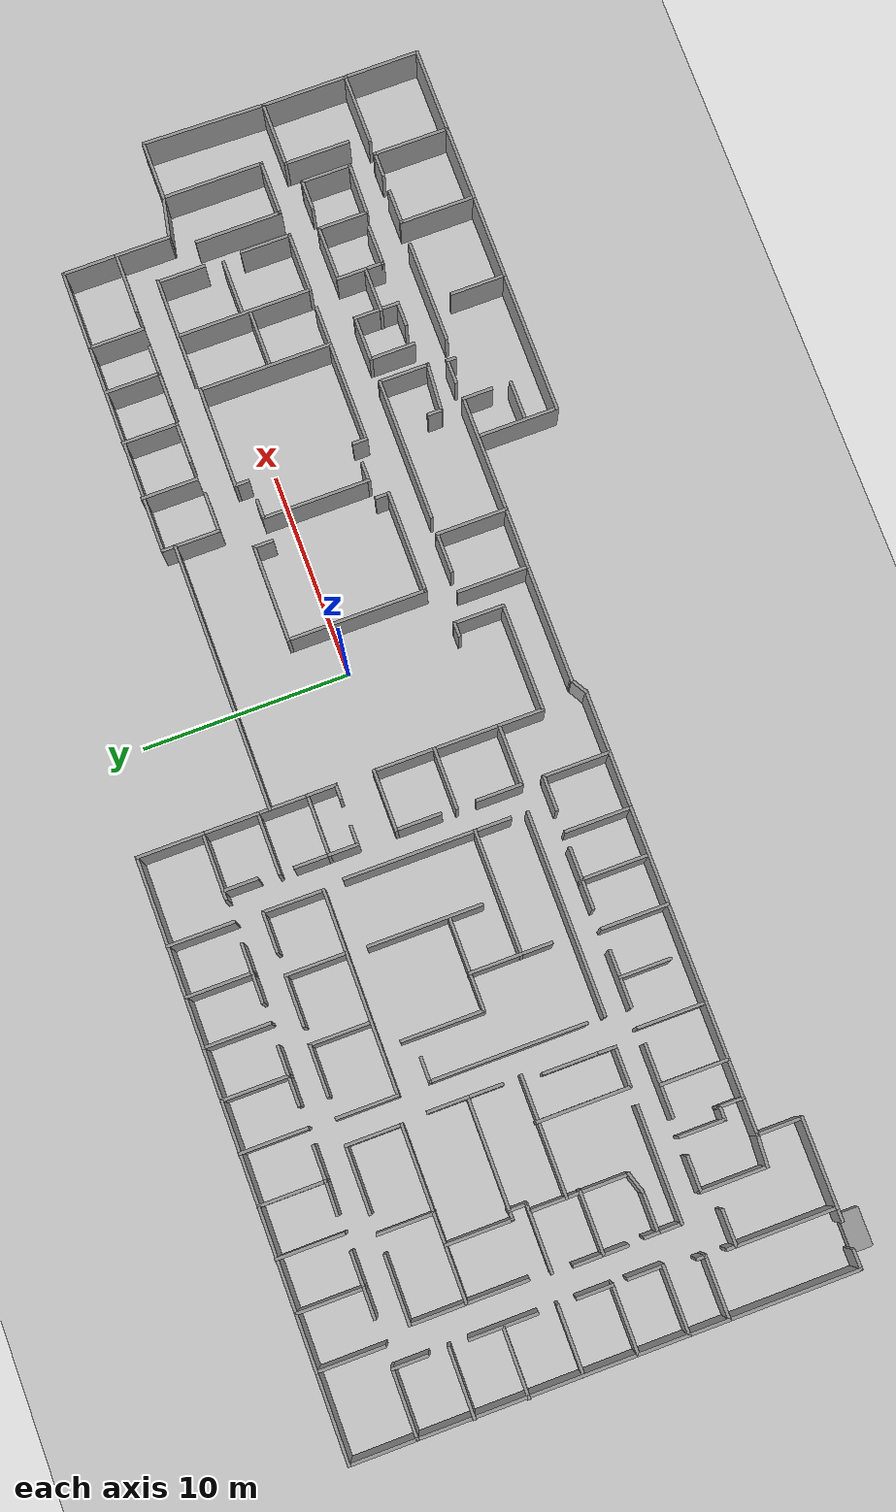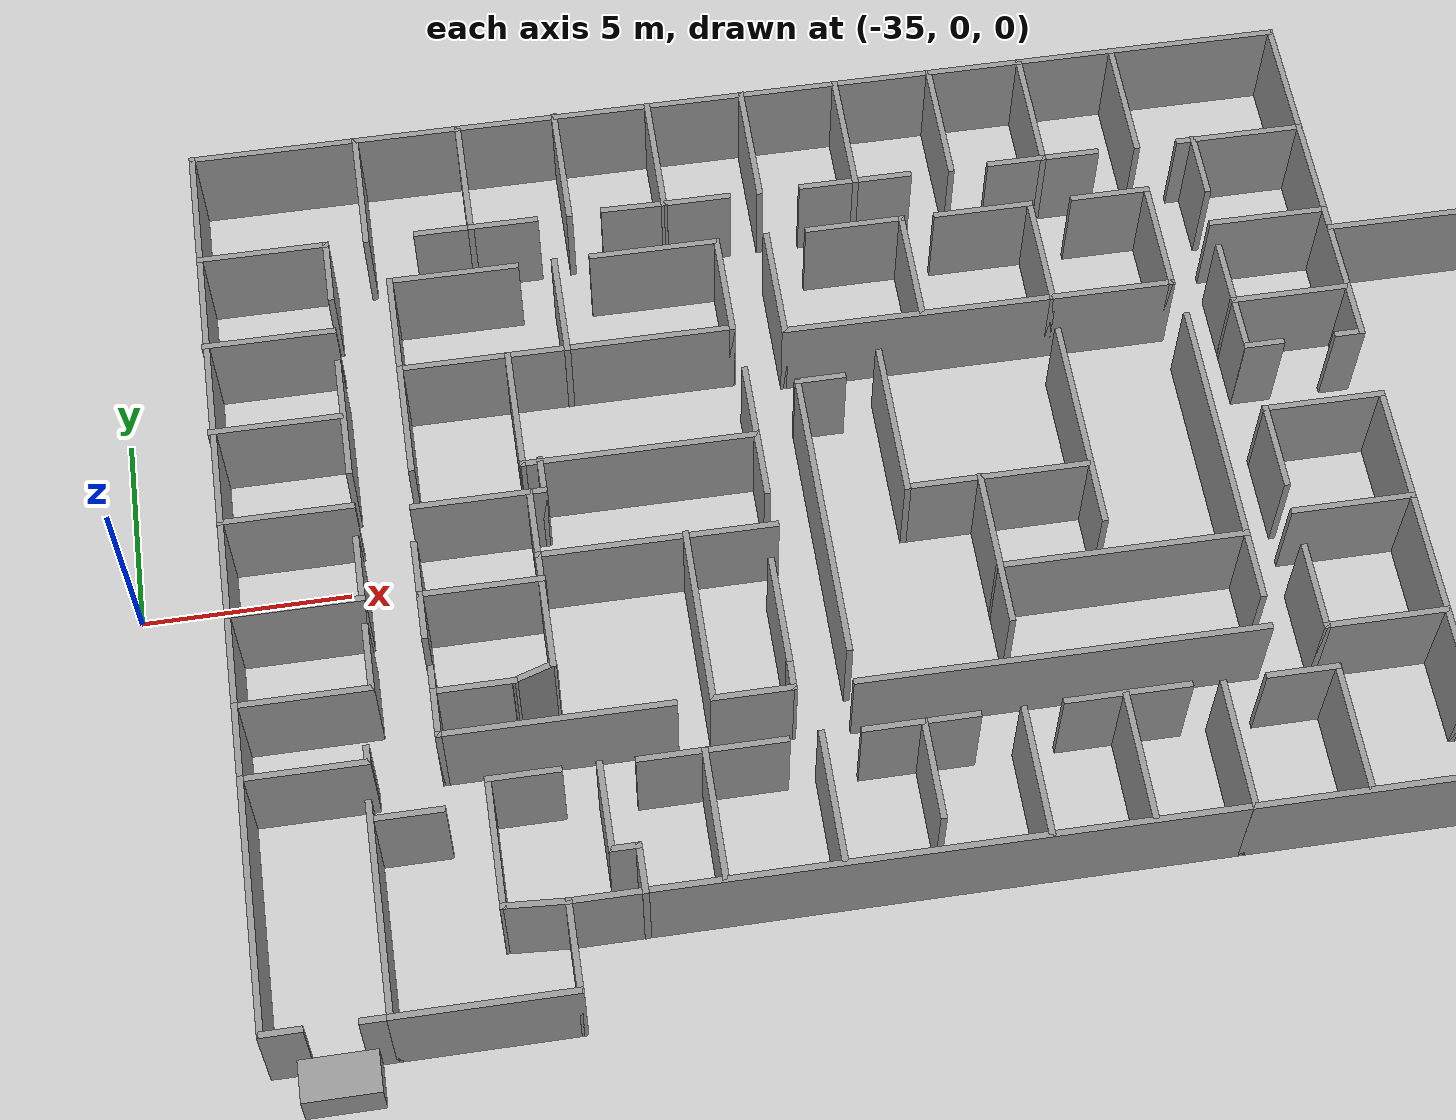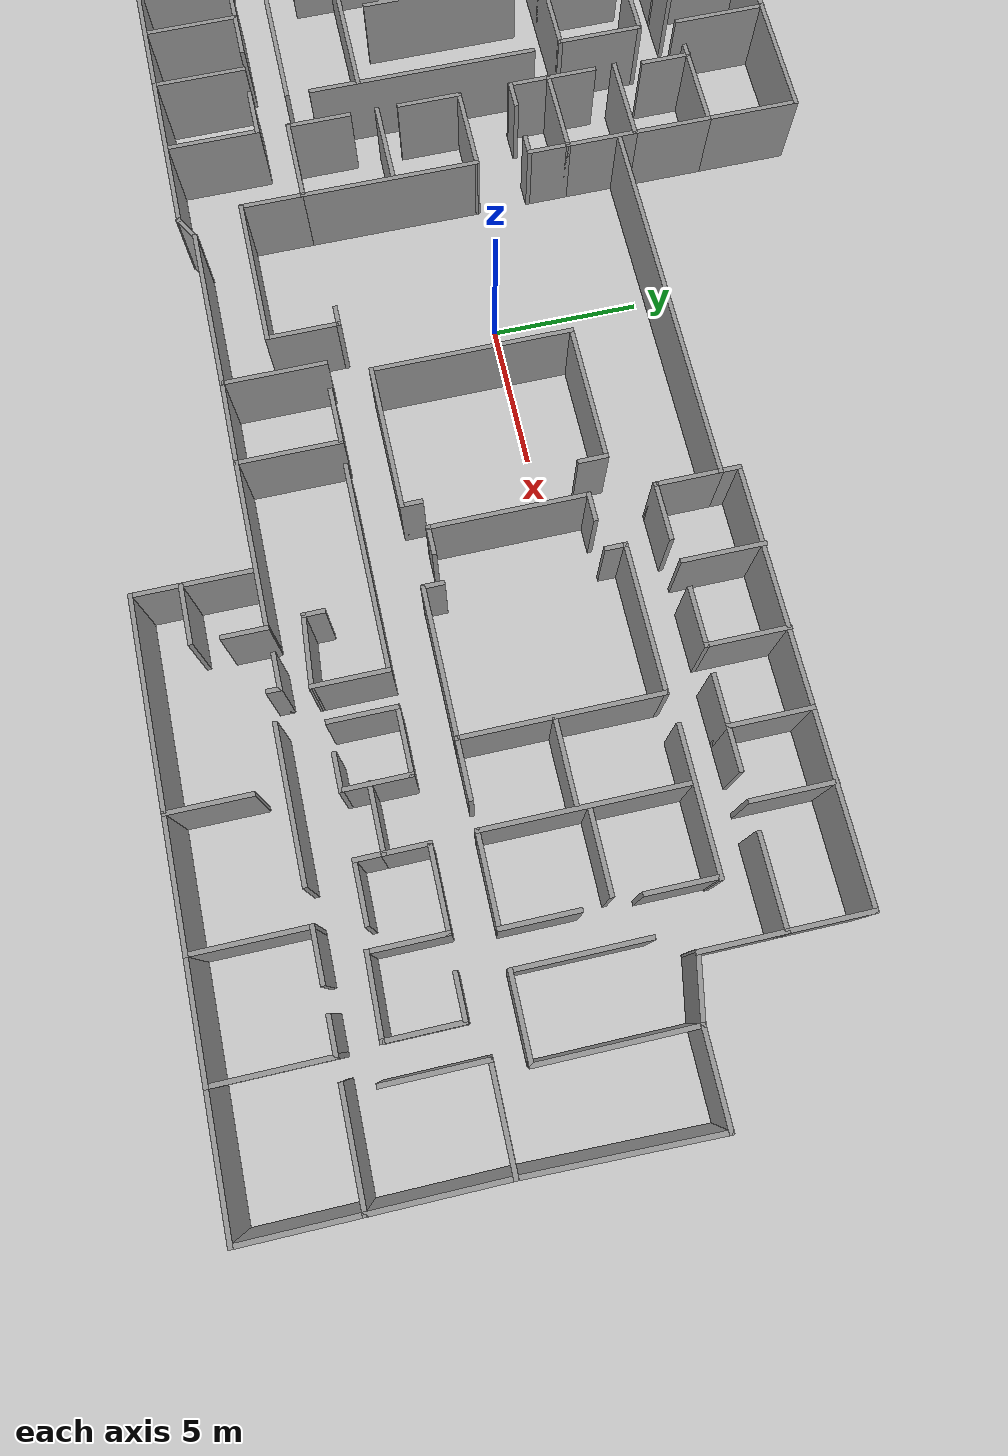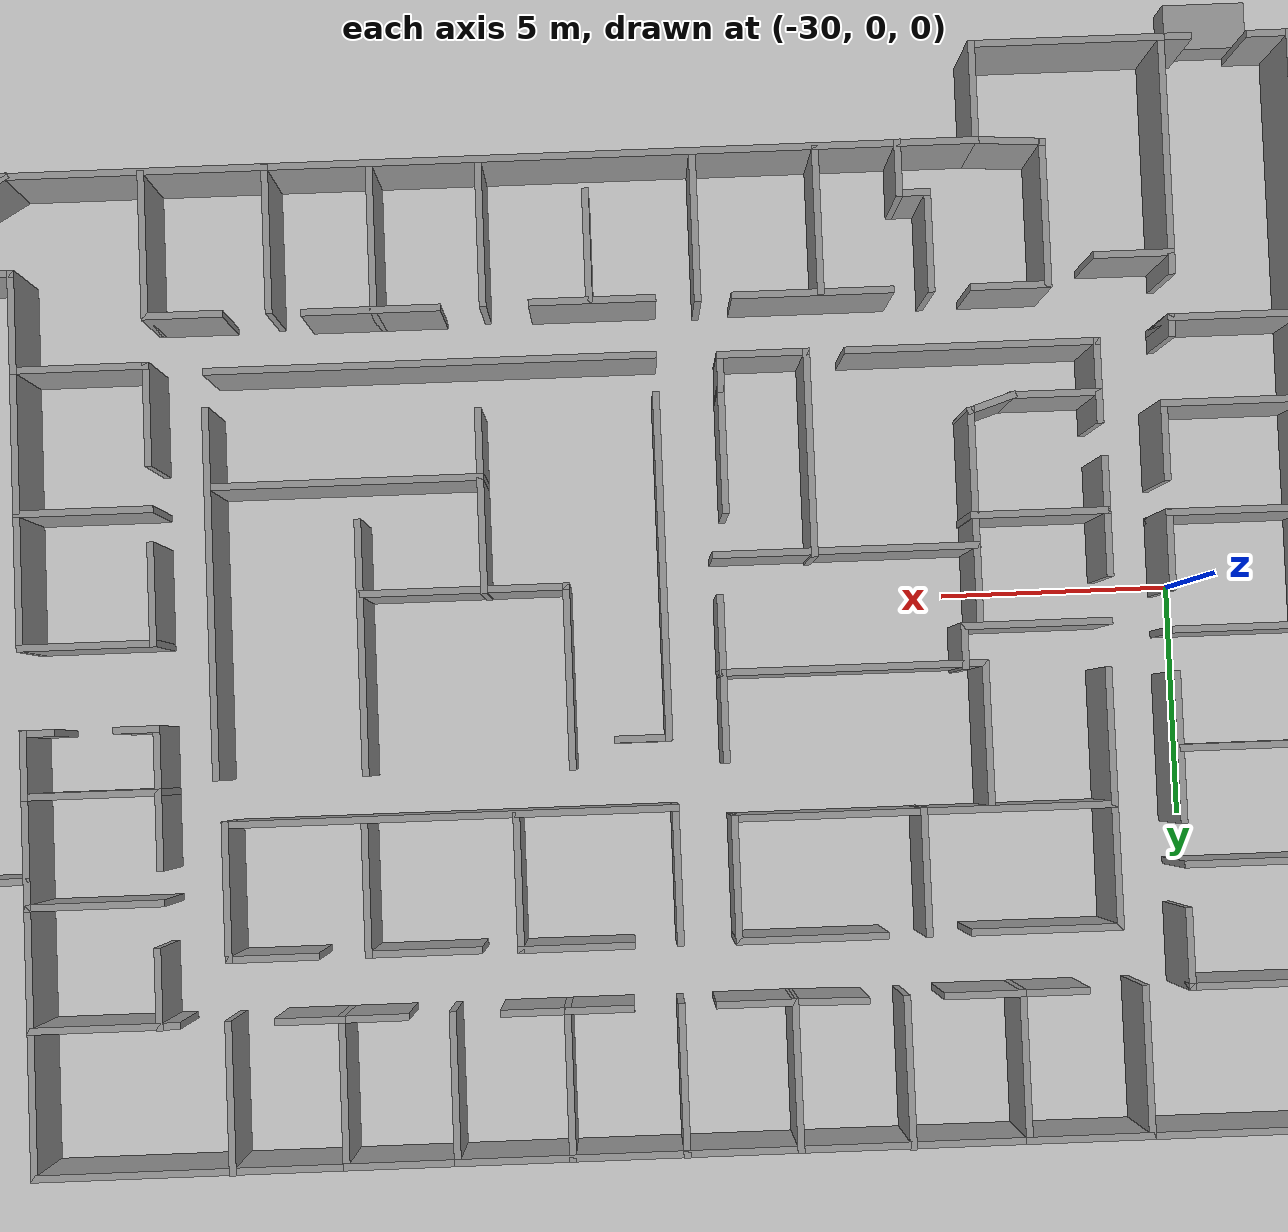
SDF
<sdf version="1.6">
 <world name="default">
  <light name="sun" type="directional">
   <pose>0 0 10 0 -0 0</pose>
   <diffuse>0.8 0.8 0.8 1</diffuse>
   <specular>0.2 0.2 0.2 1</specular>
   <attenuation>
    <range>1000</range>
    <constant>0.9</constant>
    <linear>0.01</linear>
    <quadratic>0.001</quadratic>
   </attenuation>
   <direction>-0.5 0.1 -0.9</direction>
  </light>
  <model name="ground_plane">
   <static>1</static>
   <link name="link">
    <collision name="collision">
     <geometry><plane><normal>0 0 1</normal><size>100 100</size></plane></geometry>
     <surface>
      <contact><collide_bitmask>65535</collide_bitmask></contact>
      <friction><ode><mu>100</mu><mu2>50</mu2></ode></friction>
     </surface>
    </collision>
    <visual name="visual">
     <cast_shadows>0</cast_shadows>
     <geometry><plane><normal>0 0 1</normal><size>100 100</size></plane></geometry>
     <material>
      <script><uri>file://media/materials/scripts/gazebo.material</uri><name>Gazebo/Grey</name></script>
     </material>
    </visual>
   </link>
  </model>
  <gravity>0 0 -9.8</gravity>
  <magnetic_field>6e-06 2.3e-05 -4.2e-05</magnetic_field>
  <atmosphere type="adiabatic"/>
  <physics name="default_physics" default="0" type="ode">
   <max_step_size>0.001</max_step_size>
   <real_time_factor>1</real_time_factor>
   <real_time_update_rate>1000</real_time_update_rate>
  </physics>
  <scene><ambient>0.4 0.4 0.4 1</ambient><background>0.7 0.7 0.7 1</background><shadows>1</shadows></scene>
  <audio><device>default</device></audio>
  <spherical_coordinates>
   <surface_model>EARTH_WGS84</surface_model>
   <latitude_deg>0</latitude_deg>
   <longitude_deg>0</longitude_deg>
   <elevation>0</elevation>
   <heading_deg>0</heading_deg>
  </spherical_coordinates>
  <model name="large_version">
   <pose>-3.01766 -0.701661 0 0 -0 0</pose>
   <link name="Wall_0">
    <collision name="Wall_0_Collision">
     <geometry><box><size>4.25 0.15 2.5</size></box></geometry>
     <pose>0 0 1.25 0 -0 0</pose>
    </collision>
    <visual name="Wall_0_Visual">
     <pose>0 0 1.25 0 -0 0</pose>
     <geometry><box><size>4.25 0.15 2.5</size></box></geometry>
     <material>
      <script><uri>file://media/materials/scripts/gazebo.material</uri><name>Gazebo/Grey</name></script>
      <ambient>1 1 1 1</ambient>
     </material>
     <meta><layer>0</layer></meta>
    </visual>
    <pose>-27.678 12.4158 0 0 -0 0</pose>
   </link>
   <link name="Wall_1">
    <collision name="Wall_1_Collision">
     <geometry><box><size>3.25 0.15 2.5</size></box></geometry>
     <pose>0 0 1.25 0 -0 0</pose>
    </collision>
    <visual name="Wall_1_Visual">
     <pose>0 0 1.25 0 -0 0</pose>
     <geometry><box><size>3.25 0.15 2.5</size></box></geometry>
     <material>
      <script><uri>file://media/materials/scripts/gazebo.material</uri><name>Gazebo/Grey</name></script>
      <ambient>1 1 1 1</ambient>
     </material>
     <meta><layer>0</layer></meta>
    </visual>
    <pose>-25.628 10.8658 0 0 -0 -1.5708</pose>
   </link>
   <link name="Wall_100">
    <collision name="Wall_100_Collision">
     <geometry><box><size>2 0.15 2.5</size></box></geometry>
     <pose>0 0 1.25 0 -0 0</pose>
    </collision>
    <visual name="Wall_100_Visual">
     <pose>0 0 1.25 0 -0 0</pose>
     <geometry><box><size>2 0.15 2.5</size></box></geometry>
     <material>
      <script><uri>file://media/materials/scripts/gazebo.material</uri><name>Gazebo/Grey</name></script>
      <ambient>1 1 1 1</ambient>
     </material>
     <meta><layer>0</layer></meta>
    </visual>
    <pose>-24.3238 -3.43296 0 0 -0 0</pose>
   </link>
   <link name="Wall_104">
    <collision name="Wall_104_Collision">
     <geometry><box><size>1.11552 0.15 2.5</size></box></geometry>
     <pose>0 0 1.25 0 -0 0</pose>
    </collision>
    <visual name="Wall_104_Visual">
     <pose>0 0 1.25 0 -0 0</pose>
     <geometry><box><size>1.11552 0.15 2.5</size></box></geometry>
     <material>
      <script><uri>file://media/materials/scripts/gazebo.material</uri><name>Gazebo/Grey</name></script>
      <ambient>1 1 1 1</ambient>
     </material>
     <meta><layer>0</layer></meta>
    </visual>
    <pose>-22.9396 -3.2841 0 0 -0 -2.82813</pose>
   </link>
   <link name="Wall_106">
    <collision name="Wall_106_Collision">
     <geometry><box><size>10.25 0.15 2.5</size></box></geometry>
     <pose>0 0 1.25 0 -0 0</pose>
    </collision>
    <visual name="Wall_106_Visual">
     <pose>0 0 1.25 0 -0 0</pose>
     <geometry><box><size>10.25 0.15 2.5</size></box></geometry>
     <material>
      <script><uri>file://media/materials/scripts/gazebo.material</uri><name>Gazebo/Grey</name></script>
      <ambient>1 1 1 1</ambient>
     </material>
     <meta><layer>0</layer></meta>
    </visual>
    <pose>-29.728 4.26583 0 0 -0 -1.5708</pose>
   </link>
   <link name="Wall_107">
    <collision name="Wall_107_Collision">
     <geometry><box><size>3.25 0.15 2.5</size></box></geometry>
     <pose>0 0 1.25 0 -0 0</pose>
    </collision>
    <visual name="Wall_107_Visual">
     <pose>0 0 1.25 0 -0 0</pose>
     <geometry><box><size>3.25 0.15 2.5</size></box></geometry>
     <material>
      <script><uri>file://media/materials/scripts/gazebo.material</uri><name>Gazebo/Grey</name></script>
      <ambient>1 1 1 1</ambient>
     </material>
     <meta><layer>0</layer></meta>
    </visual>
    <pose>-28.178 -0.784168 0 0 -0 0</pose>
   </link>
   <link name="Wall_108">
    <collision name="Wall_108_Collision">
     <geometry><box><size>1.75 0.15 2.5</size></box></geometry>
     <pose>0 0 1.25 0 -0 0</pose>
    </collision>
    <visual name="Wall_108_Visual">
     <pose>0 0 1.25 0 -0 0</pose>
     <geometry><box><size>1.75 0.15 2.5</size></box></geometry>
     <material>
      <script><uri>file://media/materials/scripts/gazebo.material</uri><name>Gazebo/Grey</name></script>
      <ambient>1 1 1 1</ambient>
     </material>
     <meta><layer>0</layer></meta>
    </visual>
    <pose>-26.628 0.015832 0 0 -0 1.5708</pose>
   </link>
   <link name="Wall_11">
    <collision name="Wall_11_Collision">
     <geometry><box><size>12.25 0.15 2.5</size></box></geometry>
     <pose>0 0 1.25 0 -0 0</pose>
    </collision>
    <visual name="Wall_11_Visual">
     <pose>0 0 1.25 0 -0 0</pose>
     <geometry><box><size>12.25 0.15 2.5</size></box></geometry>
     <material>
      <script><uri>file://media/materials/scripts/gazebo.material</uri><name>Gazebo/Grey</name></script>
      <ambient>1 1 1 1</ambient>
     </material>
     <meta><layer>0</layer></meta>
    </visual>
    <pose>-16.978 12.4158 0 0 -0 0</pose>
   </link>
   <link name="Wall_111">
    <collision name="Wall_111_Collision">
     <geometry><box><size>3.25 0.15 2.5</size></box></geometry>
     <pose>0 0 1.25 0 -0 0</pose>
    </collision>
    <visual name="Wall_111_Visual">
     <pose>0 0 1.25 0 -0 0</pose>
     <geometry><box><size>3.25 0.15 2.5</size></box></geometry>
     <material>
      <script><uri>file://media/materials/scripts/gazebo.material</uri><name>Gazebo/Grey</name></script>
      <ambient>1 1 1 1</ambient>
     </material>
     <meta><layer>0</layer></meta>
    </visual>
    <pose>-28.1916 1.72919 0 0 -0 3.14159</pose>
   </link>
   <link name="Wall_113">
    <collision name="Wall_113_Collision">
     <geometry><box><size>3.25 0.15 2.5</size></box></geometry>
     <pose>0 0 1.25 0 -0 0</pose>
    </collision>
    <visual name="Wall_113_Visual">
     <pose>0 0 1.25 0 -0 0</pose>
     <geometry><box><size>3.25 0.15 2.5</size></box></geometry>
     <material>
      <script><uri>file://media/materials/scripts/gazebo.material</uri><name>Gazebo/Grey</name></script>
      <ambient>1 1 1 1</ambient>
     </material>
     <meta><layer>0</layer></meta>
    </visual>
    <pose>-26.6242 4.2381 0 0 -0 1.5708</pose>
   </link>
   <link name="Wall_115">
    <collision name="Wall_115_Collision">
     <geometry><box><size>3.25 0.15 2.5</size></box></geometry>
     <pose>0 0 1.25 0 -0 0</pose>
    </collision>
    <visual name="Wall_115_Visual">
     <pose>0 0 1.25 0 -0 0</pose>
     <geometry><box><size>3.25 0.15 2.5</size></box></geometry>
     <material>
      <script><uri>file://media/materials/scripts/gazebo.material</uri><name>Gazebo/Grey</name></script>
      <ambient>1 1 1 1</ambient>
     </material>
     <meta><layer>0</layer></meta>
    </visual>
    <pose>-28.2299 4.25723 0 0 -0 0</pose>
   </link>
   <link name="Wall_117">
    <collision name="Wall_117_Collision">
     <geometry><box><size>3.25 0.15 2.5</size></box></geometry>
     <pose>0 0 1.25 0 -0 0</pose>
    </collision>
    <visual name="Wall_117_Visual">
     <pose>0 0 1.25 0 -0 0</pose>
     <geometry><box><size>3.25 0.15 2.5</size></box></geometry>
     <material>
      <script><uri>file://media/materials/scripts/gazebo.material</uri><name>Gazebo/Grey</name></script>
      <ambient>1 1 1 1</ambient>
     </material>
     <meta><layer>0</layer></meta>
    </visual>
    <pose>-28.2125 6.73297 0 0 -0 0</pose>
   </link>
   <link name="Wall_119">
    <collision name="Wall_119_Collision">
     <geometry><box><size>1.75 0.15 2.5</size></box></geometry>
     <pose>0 0 1.25 0 -0 0</pose>
    </collision>
    <visual name="Wall_119_Visual">
     <pose>0 0 1.25 0 -0 0</pose>
     <geometry><box><size>1.75 0.15 2.5</size></box></geometry>
     <material>
      <script><uri>file://media/materials/scripts/gazebo.material</uri><name>Gazebo/Grey</name></script>
      <ambient>1 1 1 1</ambient>
     </material>
     <meta><layer>0</layer></meta>
    </visual>
    <pose>-26.628 8.51583 0 0 -0 -1.5708</pose>
   </link>
   <link name="Wall_12">
    <collision name="Wall_12_Collision">
     <geometry><box><size>3.25 0.15 2.5</size></box></geometry>
     <pose>0 0 1.25 0 -0 0</pose>
    </collision>
    <visual name="Wall_12_Visual">
     <pose>0 0 1.25 0 -0 0</pose>
     <geometry><box><size>3.25 0.15 2.5</size></box></geometry>
     <material>
      <script><uri>file://media/materials/scripts/gazebo.material</uri><name>Gazebo/Grey</name></script>
      <ambient>1 1 1 1</ambient>
     </material>
     <meta><layer>0</layer></meta>
    </visual>
    <pose>-10.928 10.8658 0 0 -0 -1.5708</pose>
   </link>
   <link name="Wall_121">
    <collision name="Wall_121_Collision">
     <geometry><box><size>2.5 0.15 2.5</size></box></geometry>
     <pose>0 0 1.25 0 -0 0</pose>
    </collision>
    <visual name="Wall_121_Visual">
     <pose>0 0 1.25 0 -0 0</pose>
     <geometry><box><size>2.5 0.15 2.5</size></box></geometry>
     <material>
      <script><uri>file://media/materials/scripts/gazebo.material</uri><name>Gazebo/Grey</name></script>
      <ambient>1 1 1 1</ambient>
     </material>
     <meta><layer>0</layer></meta>
    </visual>
    <pose>-29.728 -1.95917 0 0 -0 -1.5708</pose>
   </link>
   <link name="Wall_122">
    <collision name="Wall_122_Collision">
     <geometry><box><size>3.25 0.15 2.5</size></box></geometry>
     <pose>0 0 1.25 0 -0 0</pose>
    </collision>
    <visual name="Wall_122_Visual">
     <pose>0 0 1.25 0 -0 0</pose>
     <geometry><box><size>3.25 0.15 2.5</size></box></geometry>
     <material>
      <script><uri>file://media/materials/scripts/gazebo.material</uri><name>Gazebo/Grey</name></script>
      <ambient>1 1 1 1</ambient>
     </material>
     <meta><layer>0</layer></meta>
    </visual>
    <pose>-28.178 -3.13417 0 0 -0 0</pose>
   </link>
   <link name="Wall_123">
    <collision name="Wall_123_Collision">
     <geometry><box><size>1.75 0.15 2.5</size></box></geometry>
     <pose>0 0 1.25 0 -0 0</pose>
    </collision>
    <visual name="Wall_123_Visual">
     <pose>0 0 1.25 0 -0 0</pose>
     <geometry><box><size>1.75 0.15 2.5</size></box></geometry>
     <material>
      <script><uri>file://media/materials/scripts/gazebo.material</uri><name>Gazebo/Grey</name></script>
      <ambient>1 1 1 1</ambient>
     </material>
     <meta><layer>0</layer></meta>
    </visual>
    <pose>-26.628 -2.33417 0 0 -0 1.5708</pose>
   </link>
   <link name="Wall_125">
    <collision name="Wall_125_Collision">
     <geometry><box><size>2 0.15 2.5</size></box></geometry>
     <pose>0 0 1.25 0 -0 0</pose>
    </collision>
    <visual name="Wall_125_Visual">
     <pose>0 0 1.25 0 -0 0</pose>
     <geometry><box><size>2 0.15 2.5</size></box></geometry>
     <material>
      <script><uri>file://media/materials/scripts/gazebo.material</uri><name>Gazebo/Grey</name></script>
      <ambient>1 1 1 1</ambient>
     </material>
     <meta><layer>0</layer></meta>
    </visual>
    <pose>-29.728 -4.05917 0 0 -0 -1.5708</pose>
   </link>
   <link name="Wall_126">
    <collision name="Wall_126_Collision">
     <geometry><box><size>3 0.15 2.5</size></box></geometry>
     <pose>0 0 1.25 0 -0 0</pose>
    </collision>
    <visual name="Wall_126_Visual">
     <pose>0 0 1.25 0 -0 0</pose>
     <geometry><box><size>3 0.15 2.5</size></box></geometry>
     <material>
      <script><uri>file://media/materials/scripts/gazebo.material</uri><name>Gazebo/Grey</name></script>
      <ambient>1 1 1 1</ambient>
     </material>
     <meta><layer>0</layer></meta>
    </visual>
    <pose>-28.303 -4.98417 0 0 -0 0</pose>
   </link>
   <link name="Wall_127">
    <collision name="Wall_127_Collision">
     <geometry><box><size>0.5 0.15 2.5</size></box></geometry>
     <pose>0 0 1.25 0 -0 0</pose>
    </collision>
    <visual name="Wall_127_Visual">
     <pose>0 0 1.25 0 -0 0</pose>
     <geometry><box><size>0.5 0.15 2.5</size></box></geometry>
     <material>
      <script><uri>file://media/materials/scripts/gazebo.material</uri><name>Gazebo/Grey</name></script>
      <ambient>1 1 1 1</ambient>
     </material>
     <meta><layer>0</layer></meta>
    </visual>
    <pose>-26.878 -4.80917 0 0 -0 1.5708</pose>
   </link>
   <link name="Wall_129">
    <collision name="Wall_129_Collision">
     <geometry><box><size>6.25 0.15 2.5</size></box></geometry>
     <pose>0 0 1.25 0 -0 0</pose>
    </collision>
    <visual name="Wall_129_Visual">
     <pose>0 0 1.25 0 -0 0</pose>
     <geometry><box><size>6.25 0.15 2.5</size></box></geometry>
     <material>
      <script><uri>file://media/materials/scripts/gazebo.material</uri><name>Gazebo/Grey</name></script>
      <ambient>1 1 1 1</ambient>
     </material>
     <meta><layer>0</layer></meta>
    </visual>
    <pose>-29.728 -8.03417 0 0 -0 -1.5708</pose>
   </link>
   <link name="Wall_130">
    <collision name="Wall_130_Collision">
     <geometry><box><size>1 0.15 2.5</size></box></geometry>
     <pose>0 0 1.25 0 -0 0</pose>
    </collision>
    <visual name="Wall_130_Visual">
     <pose>0 0 1.25 0 -0 0</pose>
     <geometry><box><size>1 0.15 2.5</size></box></geometry>
     <material>
      <script><uri>file://media/materials/scripts/gazebo.material</uri><name>Gazebo/Grey</name></script>
      <ambient>1 1 1 1</ambient>
     </material>
     <meta><layer>0</layer></meta>
    </visual>
    <pose>-29.303 -11.0842 0 0 -0 0</pose>
   </link>
   <link name="Wall_133">
    <collision name="Wall_133_Collision">
     <geometry><box><size>0.75 0.15 2.5</size></box></geometry>
     <pose>0 0 1.25 0 -0 0</pose>
    </collision>
    <visual name="Wall_133_Visual">
     <pose>0 0 1.25 0 -0 0</pose>
     <geometry><box><size>0.75 0.15 2.5</size></box></geometry>
     <material>
      <script><uri>file://media/materials/scripts/gazebo.material</uri><name>Gazebo/Grey</name></script>
      <ambient>1 1 1 1</ambient>
     </material>
     <meta><layer>0</layer></meta>
    </visual>
    <pose>-27.2477 -11.0917 0 0 -0 0</pose>
   </link>
   <link name="Wall_134">
    <collision name="Wall_134_Collision">
     <geometry><box><size>5.25 0.15 2.5</size></box></geometry>
     <pose>0 0 1.25 0 -0 0</pose>
    </collision>
    <visual name="Wall_134_Visual">
     <pose>0 0 1.25 0 -0 0</pose>
     <geometry><box><size>5.25 0.15 2.5</size></box></geometry>
     <material>
      <script><uri>file://media/materials/scripts/gazebo.material</uri><name>Gazebo/Grey</name></script>
      <ambient>1 1 1 1</ambient>
     </material>
     <meta><layer>0</layer></meta>
    </visual>
    <pose>-26.9477 -8.54166 0 0 -0 1.5708</pose>
   </link>
   <link name="Wall_136">
    <collision name="Wall_136_Collision">
     <geometry><box><size>4.25 0.15 2.5</size></box></geometry>
     <pose>0 0 1.25 0 -0 0</pose>
    </collision>
    <visual name="Wall_136_Visual">
     <pose>0 0 1.25 0 -0 0</pose>
     <geometry><box><size>4.25 0.15 2.5</size></box></geometry>
     <material>
      <script><uri>file://media/materials/scripts/gazebo.material</uri><name>Gazebo/Grey</name></script>
      <ambient>1 1 1 1</ambient>
     </material>
     <meta><layer>0</layer></meta>
    </visual>
    <pose>-24.8977 -11.0917 0 0 -0 0</pose>
   </link>
   <link name="Wall_137">
    <collision name="Wall_137_Collision">
     <geometry><box><size>2.25 0.15 2.5</size></box></geometry>
     <pose>0 0 1.25 0 -0 0</pose>
    </collision>
    <visual name="Wall_137_Visual">
     <pose>0 0 1.25 0 -0 0</pose>
     <geometry><box><size>2.25 0.15 2.5</size></box></geometry>
     <material>
      <script><uri>file://media/materials/scripts/gazebo.material</uri><name>Gazebo/Grey</name></script>
      <ambient>1 1 1 1</ambient>
     </material>
     <meta><layer>0</layer></meta>
    </visual>
    <pose>-22.8477 -10.0417 0 0 -0 1.5708</pose>
   </link>
   <link name="Wall_138">
    <collision name="Wall_138_Collision">
     <geometry><box><size>15.5 0.15 2.5</size></box></geometry>
     <pose>0 0 1.25 0 -0 0</pose>
    </collision>
    <visual name="Wall_138_Visual">
     <pose>0 0 1.25 0 -0 0</pose>
     <geometry><box><size>15.5 0.15 2.5</size></box></geometry>
     <material>
      <script><uri>file://media/materials/scripts/gazebo.material</uri><name>Gazebo/Grey</name></script>
      <ambient>1 1 1 1</ambient>
     </material>
     <meta><layer>0</layer></meta>
    </visual>
    <pose>-15.1727 -8.99166 0 0 -0 0</pose>
   </link>
   <link name="Wall_14">
    <collision name="Wall_14_Collision">
     <geometry><box><size>3.25 0.15 2.5</size></box></geometry>
     <pose>0 0 1.25 0 -0 0</pose>
    </collision>
    <visual name="Wall_14_Visual">
     <pose>0 0 1.25 0 -0 0</pose>
     <geometry><box><size>3.25 0.15 2.5</size></box></geometry>
     <material>
      <script><uri>file://media/materials/scripts/gazebo.material</uri><name>Gazebo/Grey</name></script>
      <ambient>1 1 1 1</ambient>
     </material>
     <meta><layer>0</layer></meta>
    </visual>
    <pose>-20.5677 10.8967 0 0 -0 -1.5708</pose>
   </link>
   <link name="Wall_140">
    <collision name="Wall_140_Collision">
     <geometry><box><size>1.75 0.15 2.5</size></box></geometry>
     <pose>0 0 1.25 0 -0 0</pose>
    </collision>
    <visual name="Wall_140_Visual">
     <pose>0 0 1.25 0 -0 0</pose>
     <geometry><box><size>1.75 0.15 2.5</size></box></geometry>
     <material>
      <script><uri>file://media/materials/scripts/gazebo.material</uri><name>Gazebo/Grey</name></script>
      <ambient>1 1 1 1</ambient>
     </material>
     <meta><layer>0</layer></meta>
    </visual>
    <pose>-26.1412 -6.39185 0 0 -0 0</pose>
   </link>
   <link name="Wall_142">
    <collision name="Wall_142_Collision">
     <geometry><box><size>3.25 0.15 2.5</size></box></geometry>
     <pose>0 0 1.25 0 -0 0</pose>
    </collision>
    <visual name="Wall_142_Visual">
     <pose>0 0 1.25 0 -0 0</pose>
     <geometry><box><size>3.25 0.15 2.5</size></box></geometry>
     <material>
      <script><uri>file://media/materials/scripts/gazebo.material</uri><name>Gazebo/Grey</name></script>
      <ambient>1 1 1 1</ambient>
     </material>
     <meta><layer>0</layer></meta>
    </visual>
    <pose>-24.273 -7.35059 0 0 -0 -1.5708</pose>
   </link>
   <link name="Wall_143">
    <collision name="Wall_143_Collision">
     <geometry><box><size>1.5782 0.15 2.5</size></box></geometry>
     <pose>0 0 1.25 0 -0 0</pose>
    </collision>
    <visual name="Wall_143_Visual">
     <pose>0 0 1.25 0 -0 0</pose>
     <geometry><box><size>1.5782 0.15 2.5</size></box></geometry>
     <material>
      <script><uri>file://media/materials/scripts/gazebo.material</uri><name>Gazebo/Grey</name></script>
      <ambient>1 1 1 1</ambient>
     </material>
     <meta><layer>0</layer></meta>
    </visual>
    <pose>-23.5603 -8.94612 0 0 -0 -0.063809</pose>
   </link>
   <link name="Wall_145">
    <collision name="Wall_145_Collision">
     <geometry><box><size>1.75 0.15 2.5</size></box></geometry>
     <pose>0 0 1.25 0 -0 0</pose>
    </collision>
    <visual name="Wall_145_Visual">
     <pose>0 0 1.25 0 -0 0</pose>
     <geometry><box><size>1.75 0.15 2.5</size></box></geometry>
     <material>
      <script><uri>file://media/materials/scripts/gazebo.material</uri><name>Gazebo/Grey</name></script>
      <ambient>1 1 1 1</ambient>
     </material>
     <meta><layer>0</layer></meta>
    </visual>
    <pose>-23.473 -5.80059 0 0 -0 0</pose>
   </link>
   <link name="Wall_147">
    <collision name="Wall_147_Collision">
     <geometry><box><size>2.25 0.15 2.5</size></box></geometry>
     <pose>0 0 1.25 0 -0 0</pose>
    </collision>
    <visual name="Wall_147_Visual">
     <pose>0 0 1.25 0 -0 0</pose>
     <geometry><box><size>2.25 0.15 2.5</size></box></geometry>
     <material>
      <script><uri>file://media/materials/scripts/gazebo.material</uri><name>Gazebo/Grey</name></script>
      <ambient>1 1 1 1</ambient>
     </material>
     <meta><layer>0</layer></meta>
    </visual>
    <pose>-21.7563 -6.85059 0 0 -0 -1.5708</pose>
   </link>
   <link name="Wall_148">
    <collision name="Wall_148_Collision">
     <geometry><box><size>0.75 0.15 2.5</size></box></geometry>
     <pose>0 0 1.25 0 -0 0</pose>
    </collision>
    <visual name="Wall_148_Visual">
     <pose>0 0 1.25 0 -0 0</pose>
     <geometry><box><size>0.75 0.15 2.5</size></box></geometry>
     <material>
      <script><uri>file://media/materials/scripts/gazebo.material</uri><name>Gazebo/Grey</name></script>
      <ambient>1 1 1 1</ambient>
     </material>
     <meta><layer>0</layer></meta>
    </visual>
    <pose>-21.4563 -7.90059 0 0 -0 0</pose>
   </link>
   <link name="Wall_149">
    <collision name="Wall_149_Collision">
     <geometry><box><size>1.25 0.15 2.5</size></box></geometry>
     <pose>0 0 1.25 0 -0 0</pose>
    </collision>
    <visual name="Wall_149_Visual">
     <pose>0 0 1.25 0 -0 0</pose>
     <geometry><box><size>1.25 0.15 2.5</size></box></geometry>
     <material>
      <script><uri>file://media/materials/scripts/gazebo.material</uri><name>Gazebo/Grey</name></script>
      <ambient>1 1 1 1</ambient>
     </material>
     <meta><layer>0</layer></meta>
    </visual>
    <pose>-21.1563 -8.45059 0 0 -0 -1.5708</pose>
   </link>
   <link name="Wall_151">
    <collision name="Wall_151_Collision">
     <geometry><box><size>3.5 0.15 2.5</size></box></geometry>
     <pose>0 0 1.25 0 -0 0</pose>
    </collision>
    <visual name="Wall_151_Visual">
     <pose>0 0 1.25 0 -0 0</pose>
     <geometry><box><size>3.5 0.15 2.5</size></box></geometry>
     <material>
      <script><uri>file://media/materials/scripts/gazebo.material</uri><name>Gazebo/Grey</name></script>
      <ambient>1 1 1 1</ambient>
     </material>
     <meta><layer>0</layer></meta>
    </visual>
    <pose>-19.202 -5.81575 0 0 -0 0</pose>
   </link>
   <link name="Wall_153">
    <collision name="Wall_153_Collision">
     <geometry><box><size>3.25 0.15 2.5</size></box></geometry>
     <pose>0 0 1.25 0 -0 0</pose>
    </collision>
    <visual name="Wall_153_Visual">
     <pose>0 0 1.25 0 -0 0</pose>
     <geometry><box><size>3.25 0.15 2.5</size></box></geometry>
     <material>
      <script><uri>file://media/materials/scripts/gazebo.material</uri><name>Gazebo/Grey</name></script>
      <ambient>1 1 1 1</ambient>
     </material>
     <meta><layer>0</layer></meta>
    </visual>
    <pose>-19.3761 -7.38091 0 0 -0 -1.5708</pose>
   </link>
   <link name="Wall_155">
    <collision name="Wall_155_Collision">
     <geometry><box><size>3.25 0.15 2.5</size></box></geometry>
     <pose>0 0 1.25 0 -0 0</pose>
    </collision>
    <visual name="Wall_155_Visual">
     <pose>0 0 1.25 0 -0 0</pose>
     <geometry><box><size>3.25 0.15 2.5</size></box></geometry>
     <material>
      <script><uri>file://media/materials/scripts/gazebo.material</uri><name>Gazebo/Grey</name></script>
      <ambient>1 1 1 1</ambient>
     </material>
     <meta><layer>0</layer></meta>
    </visual>
    <pose>-16.723 -7.33543 0 0 -0 -1.5708</pose>
   </link>
   <link name="Wall_157">
    <collision name="Wall_157_Collision">
     <geometry><box><size>2.75 0.15 2.5</size></box></geometry>
     <pose>0 0 1.25 0 -0 0</pose>
    </collision>
    <visual name="Wall_157_Visual">
     <pose>0 0 1.25 0 -0 0</pose>
     <geometry><box><size>2.75 0.15 2.5</size></box></geometry>
     <material>
      <script><uri>file://media/materials/scripts/gazebo.material</uri><name>Gazebo/Grey</name></script>
      <ambient>1 1 1 1</ambient>
     </material>
     <meta><layer>0</layer></meta>
    </visual>
    <pose>-14.4527 -5.83091 0 0 -0 0</pose>
   </link>
   <link name="Wall_159">
    <collision name="Wall_159_Collision">
     <geometry><box><size>2.5 0.15 2.5</size></box></geometry>
     <pose>0 0 1.25 0 -0 0</pose>
    </collision>
    <visual name="Wall_159_Visual">
     <pose>0 0 1.25 0 -0 0</pose>
     <geometry><box><size>2.5 0.15 2.5</size></box></geometry>
     <material>
      <script><uri>file://media/materials/scripts/gazebo.material</uri><name>Gazebo/Grey</name></script>
      <ambient>1 1 1 1</ambient>
     </material>
     <meta><layer>0</layer></meta>
    </visual>
    <pose>-14.3882 -7.02107 0 0 -0 -1.5708</pose>
   </link>
   <link name="Wall_16">
    <collision name="Wall_16_Collision">
     <geometry><box><size>3.25 0.15 2.5</size></box></geometry>
     <pose>0 0 1.25 0 -0 0</pose>
    </collision>
    <visual name="Wall_16_Visual">
     <pose>0 0 1.25 0 -0 0</pose>
     <geometry><box><size>3.25 0.15 2.5</size></box></geometry>
     <material>
      <script><uri>file://media/materials/scripts/gazebo.material</uri><name>Gazebo/Grey</name></script>
      <ambient>1 1 1 1</ambient>
     </material>
     <meta><layer>0</layer></meta>
    </visual>
    <pose>-18.1926 10.8707 0 0 -0 -1.5708</pose>
   </link>
   <link name="Wall_161">
    <collision name="Wall_161_Collision">
     <geometry><box><size>3.25 0.15 2.5</size></box></geometry>
     <pose>0 0 1.25 0 -0 0</pose>
    </collision>
    <visual name="Wall_161_Visual">
     <pose>0 0 1.25 0 -0 0</pose>
     <geometry><box><size>3.25 0.15 2.5</size></box></geometry>
     <material>
      <script><uri>file://media/materials/scripts/gazebo.material</uri><name>Gazebo/Grey</name></script>
      <ambient>1 1 1 1</ambient>
     </material>
     <meta><layer>0</layer></meta>
    </visual>
    <pose>-12.099 -7.41123 0 0 -0 -1.5708</pose>
   </link>
   <link name="Wall_163">
    <collision name="Wall_163_Collision">
     <geometry><box><size>3 0.15 2.5</size></box></geometry>
     <pose>0 0 1.25 0 -0 0</pose>
    </collision>
    <visual name="Wall_163_Visual">
     <pose>0 0 1.25 0 -0 0</pose>
     <geometry><box><size>3 0.15 2.5</size></box></geometry>
     <material>
      <script><uri>file://media/materials/scripts/gazebo.material</uri><name>Gazebo/Grey</name></script>
      <ambient>1 1 1 1</ambient>
     </material>
     <meta><layer>0</layer></meta>
    </visual>
    <pose>-9.68851 -5.80059 0 0 -0 0</pose>
   </link>
   <link name="Wall_165">
    <collision name="Wall_165_Collision">
     <geometry><box><size>3.25 0.15 2.5</size></box></geometry>
     <pose>0 0 1.25 0 -0 0</pose>
    </collision>
    <visual name="Wall_165_Visual">
     <pose>0 0 1.25 0 -0 0</pose>
     <geometry><box><size>3.25 0.15 2.5</size></box></geometry>
     <material>
      <script><uri>file://media/materials/scripts/gazebo.material</uri><name>Gazebo/Grey</name></script>
      <ambient>1 1 1 1</ambient>
     </material>
     <meta><layer>0</layer></meta>
    </visual>
    <pose>-9.74906 -7.35059 0 0 -0 -1.5708</pose>
   </link>
   <link name="Wall_167">
    <collision name="Wall_167_Collision">
     <geometry><box><size>1.75 0.15 2.5</size></box></geometry>
     <pose>0 0 1.25 0 -0 0</pose>
    </collision>
    <visual name="Wall_167_Visual">
     <pose>0 0 1.25 0 -0 0</pose>
     <geometry><box><size>1.75 0.15 2.5</size></box></geometry>
     <material>
      <script><uri>file://media/materials/scripts/gazebo.material</uri><name>Gazebo/Grey</name></script>
      <ambient>1 1 1 1</ambient>
     </material>
     <meta><layer>0</layer></meta>
    </visual>
    <pose>-5.62887 -5.84607 0 0 -0 0</pose>
   </link>
   <link name="Wall_169">
    <collision name="Wall_169_Collision">
     <geometry><box><size>3.25 0.15 2.5</size></box></geometry>
     <pose>0 0 1.25 0 -0 0</pose>
    </collision>
    <visual name="Wall_169_Visual">
     <pose>0 0 1.25 0 -0 0</pose>
     <geometry><box><size>3.25 0.15 2.5</size></box></geometry>
     <material>
      <script><uri>file://media/materials/scripts/gazebo.material</uri><name>Gazebo/Grey</name></script>
      <ambient>1 1 1 1</ambient>
     </material>
     <meta><layer>0</layer></meta>
    </visual>
    <pose>-4.82887 -7.39607 0 0 -0 -1.5708</pose>
   </link>
   <link name="Wall_171">
    <collision name="Wall_171_Collision">
     <geometry><box><size>5.75 0.15 2.5</size></box></geometry>
     <pose>0 0 1.25 0 -0 0</pose>
    </collision>
    <visual name="Wall_171_Visual">
     <pose>0 0 1.25 0 -0 0</pose>
     <geometry><box><size>5.75 0.15 2.5</size></box></geometry>
     <material>
      <script><uri>file://media/materials/scripts/gazebo.material</uri><name>Gazebo/Grey</name></script>
      <ambient>1 1 1 1</ambient>
     </material>
     <meta><layer>0</layer></meta>
    </visual>
    <pose>-4.69767 -8.99166 0 0 -0 0</pose>
   </link>
   <link name="Wall_173">
    <collision name="Wall_173_Collision">
     <geometry><box><size>3.25 0.15 2.5</size></box></geometry>
     <pose>0 0 1.25 0 -0 0</pose>
    </collision>
    <visual name="Wall_173_Visual">
     <pose>0 0 1.25 0 -0 0</pose>
     <geometry><box><size>3.25 0.15 2.5</size></box></geometry>
     <material>
      <script><uri>file://media/materials/scripts/gazebo.material</uri><name>Gazebo/Grey</name></script>
      <ambient>1 1 1 1</ambient>
     </material>
     <meta><layer>0</layer></meta>
    </visual>
    <pose>-7.49767 -7.44166 0 0 -0 1.5708</pose>
   </link>
   <link name="Wall_178">
    <collision name="Wall_178_Collision">
     <geometry><box><size>2.25 0.15 2.5</size></box></geometry>
     <pose>0 0 1.25 0 -0 0</pose>
    </collision>
    <visual name="Wall_178_Visual">
     <pose>0 0 1.25 0 -0 0</pose>
     <geometry><box><size>2.25 0.15 2.5</size></box></geometry>
     <material>
      <script><uri>file://media/materials/scripts/gazebo.material</uri><name>Gazebo/Grey</name></script>
      <ambient>1 1 1 1</ambient>
     </material>
     <meta><layer>0</layer></meta>
    </visual>
    <pose>-4.81926 -3.73255 0 0 -0 -1.5708</pose>
   </link>
   <link name="Wall_179">
    <collision name="Wall_179_Collision">
     <geometry><box><size>3 0.15 2.5</size></box></geometry>
     <pose>0 0 1.25 0 -0 0</pose>
    </collision>
    <visual name="Wall_179_Visual">
     <pose>0 0 1.25 0 -0 0</pose>
     <geometry><box><size>3 0.15 2.5</size></box></geometry>
     <material>
      <script><uri>file://media/materials/scripts/gazebo.material</uri><name>Gazebo/Grey</name></script>
      <ambient>1 1 1 1</ambient>
     </material>
     <meta><layer>0</layer></meta>
    </visual>
    <pose>-3.39426 -4.78255 0 0 -0 0</pose>
   </link>
   <link name="Wall_18">
    <collision name="Wall_18_Collision">
     <geometry><box><size>3.25 0.15 2.5</size></box></geometry>
     <pose>0 0 1.25 0 -0 0</pose>
    </collision>
    <visual name="Wall_18_Visual">
     <pose>0 0 1.25 0 -0 0</pose>
     <geometry><box><size>3.25 0.15 2.5</size></box></geometry>
     <material>
      <script><uri>file://media/materials/scripts/gazebo.material</uri><name>Gazebo/Grey</name></script>
      <ambient>1 1 1 1</ambient>
     </material>
     <meta><layer>0</layer></meta>
    </visual>
    <pose>-15.7829 10.8794 0 0 -0 -1.5708</pose>
   </link>
   <link name="Wall_181">
    <collision name="Wall_181_Collision">
     <geometry><box><size>3 0.15 2.5</size></box></geometry>
     <pose>0 0 1.25 0 -0 0</pose>
    </collision>
    <visual name="Wall_181_Visual">
     <pose>0 0 1.25 0 -0 0</pose>
     <geometry><box><size>3 0.15 2.5</size></box></geometry>
     <material>
      <script><uri>file://media/materials/scripts/gazebo.material</uri><name>Gazebo/Grey</name></script>
      <ambient>1 1 1 1</ambient>
     </material>
     <meta><layer>0</layer></meta>
    </visual>
    <pose>-3.38496 1.18797 0 0 -0 3.14159</pose>
   </link>
   <link name="Wall_182">
    <collision name="Wall_182_Collision">
     <geometry><box><size>2.25 0.15 2.5</size></box></geometry>
     <pose>0 0 1.25 0 -0 0</pose>
    </collision>
    <visual name="Wall_182_Visual">
     <pose>0 0 1.25 0 -0 0</pose>
     <geometry><box><size>2.25 0.15 2.5</size></box></geometry>
     <material>
      <script><uri>file://media/materials/scripts/gazebo.material</uri><name>Gazebo/Grey</name></script>
      <ambient>1 1 1 1</ambient>
     </material>
     <meta><layer>0</layer></meta>
    </visual>
    <pose>-4.80996 0.137968 0 0 -0 -1.5708</pose>
   </link>
   <link name="Wall_184">
    <collision name="Wall_184_Collision">
     <geometry><box><size>3 0.15 2.5</size></box></geometry>
     <pose>0 0 1.25 0 -0 0</pose>
    </collision>
    <visual name="Wall_184_Visual">
     <pose>0 0 1.25 0 -0 0</pose>
     <geometry><box><size>3 0.15 2.5</size></box></geometry>
     <material>
      <script><uri>file://media/materials/scripts/gazebo.material</uri><name>Gazebo/Grey</name></script>
      <ambient>1 1 1 1</ambient>
     </material>
     <meta><layer>0</layer></meta>
    </visual>
    <pose>-3.39426 -1.68877 0 0 -0 0</pose>
   </link>
   <link name="Wall_186">
    <collision name="Wall_186_Collision">
     <geometry><box><size>1.75 0.15 2.5</size></box></geometry>
     <pose>0 0 1.25 0 -0 0</pose>
    </collision>
    <visual name="Wall_186_Visual">
     <pose>0 0 1.25 0 -0 0</pose>
     <geometry><box><size>1.75 0.15 2.5</size></box></geometry>
     <material>
      <script><uri>file://media/materials/scripts/gazebo.material</uri><name>Gazebo/Grey</name></script>
      <ambient>1 1 1 1</ambient>
     </material>
     <meta><layer>0</layer></meta>
    </visual>
    <pose>-16.9493 1.48236 0 0 -0 -1.5708</pose>
   </link>
   <link name="Wall_188">
    <collision name="Wall_188_Collision">
     <geometry><box><size>5.75 0.15 2.5</size></box></geometry>
     <pose>0 0 1.25 0 -0 0</pose>
    </collision>
    <visual name="Wall_188_Visual">
     <pose>0 0 1.25 0 -0 0</pose>
     <geometry><box><size>5.75 0.15 2.5</size></box></geometry>
     <material>
      <script><uri>file://media/materials/scripts/gazebo.material</uri><name>Gazebo/Grey</name></script>
      <ambient>1 1 1 1</ambient>
     </material>
     <meta><layer>0</layer></meta>
    </visual>
    <pose>-19.6903 -0.240137 0 0 -0 0</pose>
   </link>
   <link name="Wall_190">
    <collision name="Wall_190_Collision">
     <geometry><box><size>1.25 0.15 2.5</size></box></geometry>
     <pose>0 0 1.25 0 -0 0</pose>
    </collision>
    <visual name="Wall_190_Visual">
     <pose>0 0 1.25 0 -0 0</pose>
     <geometry><box><size>1.25 0.15 2.5</size></box></geometry>
     <material>
      <script><uri>file://media/materials/scripts/gazebo.material</uri><name>Gazebo/Grey</name></script>
      <ambient>1 1 1 1</ambient>
     </material>
     <meta><layer>0</layer></meta>
    </visual>
    <pose>-25.2488 -3.98296 0 0 -0 -1.5708</pose>
   </link>
   <link name="Wall_191">
    <collision name="Wall_191_Collision">
     <geometry><box><size>5.5 0.15 2.5</size></box></geometry>
     <pose>0 0 1.25 0 -0 0</pose>
    </collision>
    <visual name="Wall_191_Visual">
     <pose>0 0 1.25 0 -0 0</pose>
     <geometry><box><size>5.5 0.15 2.5</size></box></geometry>
     <material>
      <script><uri>file://media/materials/scripts/gazebo.material</uri><name>Gazebo/Grey</name></script>
      <ambient>1 1 1 1</ambient>
     </material>
     <meta><layer>0</layer></meta>
    </visual>
    <pose>-22.5738 -4.53296 0 0 -0 0</pose>
   </link>
   <link name="Wall_195">
    <collision name="Wall_195_Collision">
     <geometry><box><size>4.5 0.15 2.5</size></box></geometry>
     <pose>0 0 1.25 0 -0 0</pose>
    </collision>
    <visual name="Wall_195_Visual">
     <pose>0 0 1.25 0 -0 0</pose>
     <geometry><box><size>4.5 0.15 2.5</size></box></geometry>
     <material>
      <script><uri>file://media/materials/scripts/gazebo.material</uri><name>Gazebo/Grey</name></script>
      <ambient>1 1 1 1</ambient>
     </material>
     <meta><layer>0</layer></meta>
    </visual>
    <pose>-19.007 -2.36781 0 0 -0 -1.5708</pose>
   </link>
   <link name="Wall_198">
    <collision name="Wall_198_Collision">
     <geometry><box><size>2.75 0.15 2.5</size></box></geometry>
     <pose>0 0 1.25 0 -0 0</pose>
    </collision>
    <visual name="Wall_198_Visual">
     <pose>0 0 1.25 0 -0 0</pose>
     <geometry><box><size>2.75 0.15 2.5</size></box></geometry>
     <material>
      <script><uri>file://media/materials/scripts/gazebo.material</uri><name>Gazebo/Grey</name></script>
      <ambient>1 1 1 1</ambient>
     </material>
     <meta><layer>0</layer></meta>
    </visual>
    <pose>-17.1418 -2.50105 0 0 -0 1.5708</pose>
   </link>
   <link name="Wall_20">
    <collision name="Wall_20_Collision">
     <geometry><box><size>3.25 0.15 2.5</size></box></geometry>
     <pose>0 0 1.25 0 -0 0</pose>
    </collision>
    <visual name="Wall_20_Visual">
     <pose>0 0 1.25 0 -0 0</pose>
     <geometry><box><size>3.25 0.15 2.5</size></box></geometry>
     <material>
      <script><uri>file://media/materials/scripts/gazebo.material</uri><name>Gazebo/Grey</name></script>
      <ambient>1 1 1 1</ambient>
     </material>
     <meta><layer>0</layer></meta>
    </visual>
    <pose>-13.3644 10.8707 0 0 -0 -1.5708</pose>
   </link>
   <link name="Wall_200">
    <collision name="Wall_200_Collision">
     <geometry><box><size>2 0.15 2.5</size></box></geometry>
     <pose>0 0 1.25 0 -0 0</pose>
    </collision>
    <visual name="Wall_200_Visual">
     <pose>0 0 1.25 0 -0 0</pose>
     <geometry><box><size>2 0.15 2.5</size></box></geometry>
     <material>
      <script><uri>file://media/materials/scripts/gazebo.material</uri><name>Gazebo/Grey</name></script>
      <ambient>1 1 1 1</ambient>
     </material>
     <meta><layer>0</layer></meta>
    </visual>
    <pose>-18.082 -4.54281 0 0 -0 0</pose>
   </link>
   <link name="Wall_201">
    <collision name="Wall_201_Collision">
     <geometry><box><size>0.891917 0.15 2.5</size></box></geometry>
     <pose>0 0 1.25 0 -0 0</pose>
    </collision>
    <visual name="Wall_201_Visual">
     <pose>0 0 1.25 0 -0 0</pose>
     <geometry><box><size>0.891917 0.15 2.5</size></box></geometry>
     <material>
      <script><uri>file://media/materials/scripts/gazebo.material</uri><name>Gazebo/Grey</name></script>
      <ambient>1 1 1 1</ambient>
     </material>
     <meta><layer>0</layer></meta>
    </visual>
    <pose>-17.1494 -4.17193 0 0 -0 1.55036</pose>
   </link>
   <link name="Wall_203">
    <collision name="Wall_203_Collision">
     <geometry><box><size>7.5 0.15 2.5</size></box></geometry>
     <pose>0 0 1.25 0 -0 0</pose>
    </collision>
    <visual name="Wall_203_Visual">
     <pose>0 0 1.25 0 -0 0</pose>
     <geometry><box><size>7.5 0.15 2.5</size></box></geometry>
     <material>
      <script><uri>file://media/materials/scripts/gazebo.material</uri><name>Gazebo/Grey</name></script>
      <ambient>1 1 1 1</ambient>
     </material>
     <meta><layer>0</layer></meta>
    </visual>
    <pose>-15.7452 -0.05846 0 0 -0 -1.5708</pose>
   </link>
   <link name="Wall_205">
    <collision name="Wall_205_Collision">
     <geometry><box><size>9.75 0.15 2.5</size></box></geometry>
     <pose>0 0 1.25 0 -0 0</pose>
    </collision>
    <visual name="Wall_205_Visual">
     <pose>0 0 1.25 0 -0 0</pose>
     <geometry><box><size>9.75 0.15 2.5</size></box></geometry>
     <material>
      <script><uri>file://media/materials/scripts/gazebo.material</uri><name>Gazebo/Grey</name></script>
      <ambient>1 1 1 1</ambient>
     </material>
     <meta><layer>0</layer></meta>
    </visual>
    <pose>-10.9187 -4.60345 0 0 -0 0</pose>
   </link>
   <link name="Wall_207">
    <collision name="Wall_207_Collision">
     <geometry><box><size>8 0.15 2.5</size></box></geometry>
     <pose>0 0 1.25 0 -0 0</pose>
    </collision>
    <visual name="Wall_207_Visual">
     <pose>0 0 1.25 0 -0 0</pose>
     <geometry><box><size>8 0.15 2.5</size></box></geometry>
     <material>
      <script><uri>file://media/materials/scripts/gazebo.material</uri><name>Gazebo/Grey</name></script>
      <ambient>1 1 1 1</ambient>
     </material>
     <meta><layer>0</layer></meta>
    </visual>
    <pose>-6.06687 0.16883 0 0 -0 -1.5708</pose>
   </link>
   <link name="Wall_209">
    <collision name="Wall_209_Collision">
     <geometry><box><size>6 0.15 2.5</size></box></geometry>
     <pose>0 0 1.25 0 -0 0</pose>
    </collision>
    <visual name="Wall_209_Visual">
     <pose>0 0 1.25 0 -0 0</pose>
     <geometry><box><size>6 0.15 2.5</size></box></geometry>
     <material>
      <script><uri>file://media/materials/scripts/gazebo.material</uri><name>Gazebo/Grey</name></script>
      <ambient>1 1 1 1</ambient>
     </material>
     <meta><layer>0</layer></meta>
    </visual>
    <pose>-8.99188 -2.11094 0 0 -0 3.14159</pose>
   </link>
   <link name="Wall_211">
    <collision name="Wall_211_Collision">
     <geometry><box><size>5.5 0.15 2.5</size></box></geometry>
     <pose>0 0 1.25 0 -0 0</pose>
    </collision>
    <visual name="Wall_211_Visual">
     <pose>0 0 1.25 0 -0 0</pose>
     <geometry><box><size>5.5 0.15 2.5</size></box></geometry>
     <material>
      <script><uri>file://media/materials/scripts/gazebo.material</uri><name>Gazebo/Grey</name></script>
      <ambient>1 1 1 1</ambient>
     </material>
     <meta><layer>0</layer></meta>
    </visual>
    <pose>-9.25386 1.44209 0 0 -0 -1.5708</pose>
   </link>
   <link name="Wall_213">
    <collision name="Wall_213_Collision">
     <geometry><box><size>4 0.15 2.5</size></box></geometry>
     <pose>0 0 1.25 0 -0 0</pose>
    </collision>
    <visual name="Wall_213_Visual">
     <pose>0 0 1.25 0 -0 0</pose>
     <geometry><box><size>4 0.15 2.5</size></box></geometry>
     <material>
      <script><uri>file://media/materials/scripts/gazebo.material</uri><name>Gazebo/Grey</name></script>
      <ambient>1 1 1 1</ambient>
     </material>
     <meta><layer>0</layer></meta>
    </visual>
    <pose>-13.6649 2.23218 0 0 -0 -1.5708</pose>
   </link>
   <link name="Wall_214">
    <collision name="Wall_214_Collision">
     <geometry><box><size>4.5 0.15 2.5</size></box></geometry>
     <pose>0 0 1.25 0 -0 0</pose>
    </collision>
    <visual name="Wall_214_Visual">
     <pose>0 0 1.25 0 -0 0</pose>
     <geometry><box><size>4.5 0.15 2.5</size></box></geometry>
     <material>
      <script><uri>file://media/materials/scripts/gazebo.material</uri><name>Gazebo/Grey</name></script>
      <ambient>1 1 1 1</ambient>
     </material>
     <meta><layer>0</layer></meta>
    </visual>
    <pose>-11.4899 0.307185 0 0 -0 0</pose>
   </link>
   <link name="Wall_216">
    <collision name="Wall_216_Collision">
     <geometry><box><size>4 0.15 2.5</size></box></geometry>
     <pose>0 0 1.25 0 -0 0</pose>
    </collision>
    <visual name="Wall_216_Visual">
     <pose>0 0 1.25 0 -0 0</pose>
     <geometry><box><size>4 0.15 2.5</size></box></geometry>
     <material>
      <script><uri>file://media/materials/scripts/gazebo.material</uri><name>Gazebo/Grey</name></script>
      <ambient>1 1 1 1</ambient>
     </material>
     <meta><layer>0</layer></meta>
    </visual>
    <pose>-11.9141 -1.59917 0 0 -0 -1.5708</pose>
   </link>
   <link name="Wall_218">
    <collision name="Wall_218_Collision">
     <geometry><box><size>1.25 0.15 2.5</size></box></geometry>
     <pose>0 0 1.25 0 -0 0</pose>
    </collision>
    <visual name="Wall_218_Visual">
     <pose>0 0 1.25 0 -0 0</pose>
     <geometry><box><size>1.25 0.15 2.5</size></box></geometry>
     <material>
      <script><uri>file://media/materials/scripts/gazebo.material</uri><name>Gazebo/Grey</name></script>
      <ambient>1 1 1 1</ambient>
     </material>
     <meta><layer>0</layer></meta>
    </visual>
    <pose>-15.1952 3.61654 0 0 -0 0</pose>
   </link>
   <link name="Wall_22">
    <collision name="Wall_22_Collision">
     <geometry><box><size>1.75 0.15 2.5</size></box></geometry>
     <pose>0 0 1.25 0 -0 0</pose>
    </collision>
    <visual name="Wall_22_Visual">
     <pose>0 0 1.25 0 -0 0</pose>
     <geometry><box><size>1.75 0.15 2.5</size></box></geometry>
     <material>
      <script><uri>file://media/materials/scripts/gazebo.material</uri><name>Gazebo/Grey</name></script>
      <ambient>1 1 1 1</ambient>
     </material>
     <meta><layer>0</layer></meta>
    </visual>
    <pose>-22.228 9.31583 0 0 -0 0</pose>
   </link>
   <link name="Wall_220">
    <collision name="Wall_220_Collision">
     <geometry><box><size>2.25 0.15 2.5</size></box></geometry>
     <pose>0 0 1.25 0 -0 0</pose>
    </collision>
    <visual name="Wall_220_Visual">
     <pose>0 0 1.25 0 -0 0</pose>
     <geometry><box><size>2.25 0.15 2.5</size></box></geometry>
     <material>
      <script><uri>file://media/materials/scripts/gazebo.material</uri><name>Gazebo/Grey</name></script>
      <ambient>1 1 1 1</ambient>
     </material>
     <meta><layer>0</layer></meta>
    </visual>
    <pose>-1.96926 -5.83255 0 0 -0 -1.5708</pose>
   </link>
   <link name="Wall_221">
    <collision name="Wall_221_Collision">
     <geometry><box><size>5.25 0.15 2.5</size></box></geometry>
     <pose>0 0 1.25 0 -0 0</pose>
    </collision>
    <visual name="Wall_221_Visual">
     <pose>0 0 1.25 0 -0 0</pose>
     <geometry><box><size>5.25 0.15 2.5</size></box></geometry>
     <material>
      <script><uri>file://media/materials/scripts/gazebo.material</uri><name>Gazebo/Grey</name></script>
      <ambient>1 1 1 1</ambient>
     </material>
     <meta><layer>0</layer></meta>
    </visual>
    <pose>0.58074 -6.88255 0 0 -0 0</pose>
   </link>
   <link name="Wall_222">
    <collision name="Wall_222_Collision">
     <geometry><box><size>2.5 0.15 2.5</size></box></geometry>
     <pose>0 0 1.25 0 -0 0</pose>
    </collision>
    <visual name="Wall_222_Visual">
     <pose>0 0 1.25 0 -0 0</pose>
     <geometry><box><size>2.5 0.15 2.5</size></box></geometry>
     <material>
      <script><uri>file://media/materials/scripts/gazebo.material</uri><name>Gazebo/Grey</name></script>
      <ambient>1 1 1 1</ambient>
     </material>
     <meta><layer>0</layer></meta>
    </visual>
    <pose>3.13074 -5.70755 0 0 -0 1.5708</pose>
   </link>
   <link name="Wall_223">
    <collision name="Wall_223_Collision">
     <geometry><box><size>0.75 0.15 2.5</size></box></geometry>
     <pose>0 0 1.25 0 -0 0</pose>
    </collision>
    <visual name="Wall_223_Visual">
     <pose>0 0 1.25 0 -0 0</pose>
     <geometry><box><size>0.75 0.15 2.5</size></box></geometry>
     <material>
      <script><uri>file://media/materials/scripts/gazebo.material</uri><name>Gazebo/Grey</name></script>
      <ambient>1 1 1 1</ambient>
     </material>
     <meta><layer>0</layer></meta>
    </visual>
    <pose>2.83074 -4.53255 0 0 -0 3.14159</pose>
   </link>
   <link name="Wall_225">
    <collision name="Wall_225_Collision">
     <geometry><box><size>6.12052 0.15 2.5</size></box></geometry>
     <pose>0 0 1.25 0 -0 0</pose>
    </collision>
    <visual name="Wall_225_Visual">
     <pose>0 0 1.25 0 -0 0</pose>
     <geometry><box><size>6.12052 0.15 2.5</size></box></geometry>
     <material>
      <script><uri>file://media/materials/scripts/gazebo.material</uri><name>Gazebo/Grey</name></script>
      <ambient>1 1 1 1</ambient>
     </material>
     <meta><layer>0</layer></meta>
    </visual>
    <pose>-1.96461 -1.79729 0 0 -0 -1.57235</pose>
   </link>
   <link name="Wall_227">
    <collision name="Wall_227_Collision">
     <geometry><box><size>13 0.15 2.5</size></box></geometry>
     <pose>0 0 1.25 0 -0 0</pose>
    </collision>
    <visual name="Wall_227_Visual">
     <pose>0 0 1.25 0 -0 0</pose>
     <geometry><box><size>13 0.15 2.5</size></box></geometry>
     <material>
      <script><uri>file://media/materials/scripts/gazebo.material</uri><name>Gazebo/Grey</name></script>
      <ambient>1 1 1 1</ambient>
     </material>
     <meta><layer>0</layer></meta>
    </visual>
    <pose>4.4619 6.1501 0 0 -0 0</pose>
   </link>
   <link name="Wall_229">
    <collision name="Wall_229_Collision">
     <geometry><box><size>0.75 0.15 2.5</size></box></geometry>
     <pose>0 0 1.25 0 -0 0</pose>
    </collision>
    <visual name="Wall_229_Visual">
     <pose>0 0 1.25 0 -0 0</pose>
     <geometry><box><size>0.75 0.15 2.5</size></box></geometry>
     <material>
      <script><uri>file://media/materials/scripts/gazebo.material</uri><name>Gazebo/Grey</name></script>
      <ambient>1 1 1 1</ambient>
     </material>
     <meta><layer>0</layer></meta>
    </visual>
    <pose>10.8869 6.4501 0 0 -0 1.5708</pose>
   </link>
   <link name="Wall_230">
    <collision name="Wall_230_Collision">
     <geometry><box><size>14.25 0.15 2.5</size></box></geometry>
     <pose>0 0 1.25 0 -0 0</pose>
    </collision>
    <visual name="Wall_230_Visual">
     <pose>0 0 1.25 0 -0 0</pose>
     <geometry><box><size>14.25 0.15 2.5</size></box></geometry>
     <material>
      <script><uri>file://media/materials/scripts/gazebo.material</uri><name>Gazebo/Grey</name></script>
      <ambient>1 1 1 1</ambient>
     </material>
     <meta><layer>0</layer></meta>
    </visual>
    <pose>17.9369 6.7501 0 0 -0 0</pose>
   </link>
   <link name="Wall_231">
    <collision name="Wall_231_Collision">
     <geometry><box><size>2.75 0.15 2.5</size></box></geometry>
     <pose>0 0 1.25 0 -0 0</pose>
    </collision>
    <visual name="Wall_231_Visual">
     <pose>0 0 1.25 0 -0 0</pose>
     <geometry><box><size>2.75 0.15 2.5</size></box></geometry>
     <material>
      <script><uri>file://media/materials/scripts/gazebo.material</uri><name>Gazebo/Grey</name></script>
      <ambient>1 1 1 1</ambient>
     </material>
     <meta><layer>0</layer></meta>
    </visual>
    <pose>24.9869 5.4501 0 0 -0 -1.5708</pose>
   </link>
   <link name="Wall_232">
    <collision name="Wall_232_Collision">
     <geometry><box><size>3 0.15 2.5</size></box></geometry>
     <pose>0 0 1.25 0 -0 0</pose>
    </collision>
    <visual name="Wall_232_Visual">
     <pose>0 0 1.25 0 -0 0</pose>
     <geometry><box><size>3 0.15 2.5</size></box></geometry>
     <material>
      <script><uri>file://media/materials/scripts/gazebo.material</uri><name>Gazebo/Grey</name></script>
      <ambient>1 1 1 1</ambient>
     </material>
     <meta><layer>0</layer></meta>
    </visual>
    <pose>23.5619 4.1501 0 0 -0 3.14159</pose>
   </link>
   <link name="Wall_234">
    <collision name="Wall_234_Collision">
     <geometry><box><size>2.75 0.15 2.5</size></box></geometry>
     <pose>0 0 1.25 0 -0 0</pose>
    </collision>
    <visual name="Wall_234_Visual">
     <pose>0 0 1.25 0 -0 0</pose>
     <geometry><box><size>2.75 0.15 2.5</size></box></geometry>
     <material>
      <script><uri>file://media/materials/scripts/gazebo.material</uri><name>Gazebo/Grey</name></script>
      <ambient>1 1 1 1</ambient>
     </material>
     <meta><layer>0</layer></meta>
    </visual>
    <pose>21.182 5.45872 0 0 -0 -1.5708</pose>
   </link>
   <link name="Wall_236">
    <collision name="Wall_236_Collision">
     <geometry><box><size>2.75 0.15 2.5</size></box></geometry>
     <pose>0 0 1.25 0 -0 0</pose>
    </collision>
    <visual name="Wall_236_Visual">
     <pose>0 0 1.25 0 -0 0</pose>
     <geometry><box><size>2.75 0.15 2.5</size></box></geometry>
     <material>
      <script><uri>file://media/materials/scripts/gazebo.material</uri><name>Gazebo/Grey</name></script>
      <ambient>1 1 1 1</ambient>
     </material>
     <meta><layer>0</layer></meta>
    </visual>
    <pose>18.8863 5.44713 0 0 -0 -1.5708</pose>
   </link>
   <link name="Wall_238">
    <collision name="Wall_238_Collision">
     <geometry><box><size>2.75 0.15 2.5</size></box></geometry>
     <pose>0 0 1.25 0 -0 0</pose>
    </collision>
    <visual name="Wall_238_Visual">
     <pose>0 0 1.25 0 -0 0</pose>
     <geometry><box><size>2.75 0.15 2.5</size></box></geometry>
     <material>
      <script><uri>file://media/materials/scripts/gazebo.material</uri><name>Gazebo/Grey</name></script>
      <ambient>1 1 1 1</ambient>
     </material>
     <meta><layer>0</layer></meta>
    </visual>
    <pose>16.324 5.48191 0 0 -0 -1.5708</pose>
   </link>
   <link name="Wall_24">
    <collision name="Wall_24_Collision">
     <geometry><box><size>1.65843 0.15 2.5</size></box></geometry>
     <pose>0 0 1.25 0 -0 0</pose>
    </collision>
    <visual name="Wall_24_Visual">
     <pose>0 0 1.25 0 -0 0</pose>
     <geometry><box><size>1.65843 0.15 2.5</size></box></geometry>
     <material>
      <script><uri>file://media/materials/scripts/gazebo.material</uri><name>Gazebo/Grey</name></script>
      <ambient>1 1 1 1</ambient>
     </material>
     <meta><layer>0</layer></meta>
    </visual>
    <pose>-18.9467 9.33213 0 0 -0 -0.015118</pose>
   </link>
   <link name="Wall_240">
    <collision name="Wall_240_Collision">
     <geometry><box><size>2.75 0.15 2.5</size></box></geometry>
     <pose>0 0 1.25 0 -0 0</pose>
    </collision>
    <visual name="Wall_240_Visual">
     <pose>0 0 1.25 0 -0 0</pose>
     <geometry><box><size>2.75 0.15 2.5</size></box></geometry>
     <material>
      <script><uri>file://media/materials/scripts/gazebo.material</uri><name>Gazebo/Grey</name></script>
      <ambient>1 1 1 1</ambient>
     </material>
     <meta><layer>0</layer></meta>
    </visual>
    <pose>13.5414 5.5051 0 0 -0 -1.5708</pose>
   </link>
   <link name="Wall_242">
    <collision name="Wall_242_Collision">
     <geometry><box><size>2.25 0.15 2.5</size></box></geometry>
     <pose>0 0 1.25 0 -0 0</pose>
    </collision>
    <visual name="Wall_242_Visual">
     <pose>0 0 1.25 0 -0 0</pose>
     <geometry><box><size>2.25 0.15 2.5</size></box></geometry>
     <material>
      <script><uri>file://media/materials/scripts/gazebo.material</uri><name>Gazebo/Grey</name></script>
      <ambient>1 1 1 1</ambient>
     </material>
     <meta><layer>0</layer></meta>
    </visual>
    <pose>10.8869 5.1001 0 0 -0 -1.5708</pose>
   </link>
   <link name="Wall_243">
    <collision name="Wall_243_Collision">
     <geometry><box><size>2 0.15 2.5</size></box></geometry>
     <pose>0 0 1.25 0 -0 0</pose>
    </collision>
    <visual name="Wall_243_Visual">
     <pose>0 0 1.25 0 -0 0</pose>
     <geometry><box><size>2 0.15 2.5</size></box></geometry>
     <material>
      <script><uri>file://media/materials/scripts/gazebo.material</uri><name>Gazebo/Grey</name></script>
      <ambient>1 1 1 1</ambient>
     </material>
     <meta><layer>0</layer></meta>
    </visual>
    <pose>11.8119 4.0501 0 0 -0 0</pose>
   </link>
   <link name="Wall_245">
    <collision name="Wall_245_Collision">
     <geometry><box><size>2 0.15 2.5</size></box></geometry>
     <pose>0 0 1.25 0 -0 0</pose>
    </collision>
    <visual name="Wall_245_Visual">
     <pose>0 0 1.25 0 -0 0</pose>
     <geometry><box><size>2 0.15 2.5</size></box></geometry>
     <material>
      <script><uri>file://media/materials/scripts/gazebo.material</uri><name>Gazebo/Grey</name></script>
      <ambient>1 1 1 1</ambient>
     </material>
     <meta><layer>0</layer></meta>
    </visual>
    <pose>15.399 4.18191 0 0 -0 3.14159</pose>
   </link>
   <link name="Wall_247">
    <collision name="Wall_247_Collision">
     <geometry><box><size>1.75 0.15 2.5</size></box></geometry>
     <pose>0 0 1.25 0 -0 0</pose>
    </collision>
    <visual name="Wall_247_Visual">
     <pose>0 0 1.25 0 -0 0</pose>
     <geometry><box><size>1.75 0.15 2.5</size></box></geometry>
     <material>
      <script><uri>file://media/materials/scripts/gazebo.material</uri><name>Gazebo/Grey</name></script>
      <ambient>1 1 1 1</ambient>
     </material>
     <meta><layer>0</layer></meta>
    </visual>
    <pose>18.0863 4.14713 0 0 -0 3.14159</pose>
   </link>
   <link name="Wall_249">
    <collision name="Wall_249_Collision">
     <geometry><box><size>1.5 0.15 2.5</size></box></geometry>
     <pose>0 0 1.25 0 -0 0</pose>
    </collision>
    <visual name="Wall_249_Visual">
     <pose>0 0 1.25 0 -0 0</pose>
     <geometry><box><size>1.5 0.15 2.5</size></box></geometry>
     <material>
      <script><uri>file://media/materials/scripts/gazebo.material</uri><name>Gazebo/Grey</name></script>
      <ambient>1 1 1 1</ambient>
     </material>
     <meta><layer>0</layer></meta>
    </visual>
    <pose>19.5613 4.14713 0 0 -0 0</pose>
   </link>
   <link name="Wall_251">
    <collision name="Wall_251_Collision">
     <geometry><box><size>4.75 0.15 2.5</size></box></geometry>
     <pose>0 0 1.25 0 -0 0</pose>
    </collision>
    <visual name="Wall_251_Visual">
     <pose>0 0 1.25 0 -0 0</pose>
     <geometry><box><size>4.75 0.15 2.5</size></box></geometry>
     <material>
      <script><uri>file://media/materials/scripts/gazebo.material</uri><name>Gazebo/Grey</name></script>
      <ambient>1 1 1 1</ambient>
     </material>
     <meta><layer>0</layer></meta>
    </visual>
    <pose>7.30798 2.78184 0 0 -0 0</pose>
   </link>
   <link name="Wall_252">
    <collision name="Wall_252_Collision">
     <geometry><box><size>1 0.15 2.5</size></box></geometry>
     <pose>0 0 1.25 0 -0 0</pose>
    </collision>
    <visual name="Wall_252_Visual">
     <pose>0 0 1.25 0 -0 0</pose>
     <geometry><box><size>1 0.15 2.5</size></box></geometry>
     <material>
      <script><uri>file://media/materials/scripts/gazebo.material</uri><name>Gazebo/Grey</name></script>
      <ambient>1 1 1 1</ambient>
     </material>
     <meta><layer>0</layer></meta>
    </visual>
    <pose>9.60798 2.35684 0 0 -0 -1.5708</pose>
   </link>
   <link name="Wall_254">
    <collision name="Wall_254_Collision">
     <geometry><box><size>6.75 0.15 2.5</size></box></geometry>
     <pose>0 0 1.25 0 -0 0</pose>
    </collision>
    <visual name="Wall_254_Visual">
     <pose>0 0 1.25 0 -0 0</pose>
     <geometry><box><size>6.75 0.15 2.5</size></box></geometry>
     <material>
      <script><uri>file://media/materials/scripts/gazebo.material</uri><name>Gazebo/Grey</name></script>
      <ambient>1 1 1 1</ambient>
     </material>
     <meta><layer>0</layer></meta>
    </visual>
    <pose>5.00798 -0.518157 0 0 -0 -1.5708</pose>
   </link>
   <link name="Wall_255">
    <collision name="Wall_255_Collision">
     <geometry><box><size>5 0.15 2.5</size></box></geometry>
     <pose>0 0 1.25 0 -0 0</pose>
    </collision>
    <visual name="Wall_255_Visual">
     <pose>0 0 1.25 0 -0 0</pose>
     <geometry><box><size>5 0.15 2.5</size></box></geometry>
     <material>
      <script><uri>file://media/materials/scripts/gazebo.material</uri><name>Gazebo/Grey</name></script>
      <ambient>1 1 1 1</ambient>
     </material>
     <meta><layer>0</layer></meta>
    </visual>
    <pose>7.43298 -3.81816 0 0 -0 0</pose>
   </link>
   <link name="Wall_256">
    <collision name="Wall_256_Collision">
     <geometry><box><size>0.75 0.15 2.5</size></box></geometry>
     <pose>0 0 1.25 0 -0 0</pose>
    </collision>
    <visual name="Wall_256_Visual">
     <pose>0 0 1.25 0 -0 0</pose>
     <geometry><box><size>0.75 0.15 2.5</size></box></geometry>
     <material>
      <script><uri>file://media/materials/scripts/gazebo.material</uri><name>Gazebo/Grey</name></script>
      <ambient>1 1 1 1</ambient>
     </material>
     <meta><layer>0</layer></meta>
    </visual>
    <pose>9.85798 -3.51816 0 0 -0 1.5708</pose>
   </link>
   <link name="Wall_258">
    <collision name="Wall_258_Collision">
     <geometry><box><size>5.25 0.15 2.5</size></box></geometry>
     <pose>0 0 1.25 0 -0 0</pose>
    </collision>
    <visual name="Wall_258_Visual">
     <pose>0 0 1.25 0 -0 0</pose>
     <geometry><box><size>5.25 0.15 2.5</size></box></geometry>
     <material>
      <script><uri>file://media/materials/scripts/gazebo.material</uri><name>Gazebo/Grey</name></script>
      <ambient>1 1 1 1</ambient>
     </material>
     <meta><layer>0</layer></meta>
    </visual>
    <pose>10.758 -0.617491 0 0 -0 1.5708</pose>
   </link>
   <link name="Wall_26">
    <collision name="Wall_26_Collision">
     <geometry><box><size>1.75 0.15 2.5</size></box></geometry>
     <pose>0 0 1.25 0 -0 0</pose>
    </collision>
    <visual name="Wall_26_Visual">
     <pose>0 0 1.25 0 -0 0</pose>
     <geometry><box><size>1.75 0.15 2.5</size></box></geometry>
     <material>
      <script><uri>file://media/materials/scripts/gazebo.material</uri><name>Gazebo/Grey</name></script>
      <ambient>1 1 1 1</ambient>
     </material>
     <meta><layer>0</layer></meta>
    </visual>
    <pose>-17.3926 9.32072 0 0 -0 0</pose>
   </link>
   <link name="Wall_261">
    <collision name="Wall_261_Collision">
     <geometry><box><size>1 0.15 2.5</size></box></geometry>
     <pose>0 0 1.25 0 -0 0</pose>
    </collision>
    <visual name="Wall_261_Visual">
     <pose>0 0 1.25 0 -0 0</pose>
     <geometry><box><size>1 0.15 2.5</size></box></geometry>
     <material>
      <script><uri>file://media/materials/scripts/gazebo.material</uri><name>Gazebo/Grey</name></script>
      <ambient>1 1 1 1</ambient>
     </material>
     <meta><layer>0</layer></meta>
    </visual>
    <pose>11.183 1.93251 0 0 -0 0</pose>
   </link>
   <link name="Wall_263">
    <collision name="Wall_263_Collision">
     <geometry><box><size>1 0.15 2.5</size></box></geometry>
     <pose>0 0 1.25 0 -0 0</pose>
    </collision>
    <visual name="Wall_263_Visual">
     <pose>0 0 1.25 0 -0 0</pose>
     <geometry><box><size>1 0.15 2.5</size></box></geometry>
     <material>
      <script><uri>file://media/materials/scripts/gazebo.material</uri><name>Gazebo/Grey</name></script>
      <ambient>1 1 1 1</ambient>
     </material>
     <meta><layer>0</layer></meta>
    </visual>
    <pose>11.183 -3.16749 0 0 -0 0</pose>
   </link>
   <link name="Wall_265">
    <collision name="Wall_265_Collision">
     <geometry><box><size>0.75 0.15 2.5</size></box></geometry>
     <pose>0 0 1.25 0 -0 0</pose>
    </collision>
    <visual name="Wall_265_Visual">
     <pose>0 0 1.25 0 -0 0</pose>
     <geometry><box><size>0.75 0.15 2.5</size></box></geometry>
     <material>
      <script><uri>file://media/materials/scripts/gazebo.material</uri><name>Gazebo/Grey</name></script>
      <ambient>1 1 1 1</ambient>
     </material>
     <meta><layer>0</layer></meta>
    </visual>
    <pose>12.644 -3.42149 0 0 -0 -1.5708</pose>
   </link>
   <link name="Wall_267">
    <collision name="Wall_267_Collision">
     <geometry><box><size>5 0.15 2.5</size></box></geometry>
     <pose>0 0 1.25 0 -0 0</pose>
    </collision>
    <visual name="Wall_267_Visual">
     <pose>0 0 1.25 0 -0 0</pose>
     <geometry><box><size>5 0.15 2.5</size></box></geometry>
     <material>
      <script><uri>file://media/materials/scripts/gazebo.material</uri><name>Gazebo/Grey</name></script>
      <ambient>1 1 1 1</ambient>
     </material>
     <meta><layer>0</layer></meta>
    </visual>
    <pose>15.069 -3.72149 0 0 -0 0</pose>
   </link>
   <link name="Wall_268">
    <collision name="Wall_268_Collision">
     <geometry><box><size>6.5 0.15 2.5</size></box></geometry>
     <pose>0 0 1.25 0 -0 0</pose>
    </collision>
    <visual name="Wall_268_Visual">
     <pose>0 0 1.25 0 -0 0</pose>
     <geometry><box><size>6.5 0.15 2.5</size></box></geometry>
     <material>
      <script><uri>file://media/materials/scripts/gazebo.material</uri><name>Gazebo/Grey</name></script>
      <ambient>1 1 1 1</ambient>
     </material>
     <meta><layer>0</layer></meta>
    </visual>
    <pose>17.494 -0.546491 0 0 -0 1.5708</pose>
   </link>
   <link name="Wall_269">
    <collision name="Wall_269_Collision">
     <geometry><box><size>5 0.15 2.5</size></box></geometry>
     <pose>0 0 1.25 0 -0 0</pose>
    </collision>
    <visual name="Wall_269_Visual">
     <pose>0 0 1.25 0 -0 0</pose>
     <geometry><box><size>5 0.15 2.5</size></box></geometry>
     <material>
      <script><uri>file://media/materials/scripts/gazebo.material</uri><name>Gazebo/Grey</name></script>
      <ambient>1 1 1 1</ambient>
     </material>
     <meta><layer>0</layer></meta>
    </visual>
    <pose>15.069 2.62851 0 0 -0 3.14159</pose>
   </link>
   <link name="Wall_270">
    <collision name="Wall_270_Collision">
     <geometry><box><size>0.75 0.15 2.5</size></box></geometry>
     <pose>0 0 1.25 0 -0 0</pose>
    </collision>
    <visual name="Wall_270_Visual">
     <pose>0 0 1.25 0 -0 0</pose>
     <geometry><box><size>0.75 0.15 2.5</size></box></geometry>
     <material>
      <script><uri>file://media/materials/scripts/gazebo.material</uri><name>Gazebo/Grey</name></script>
      <ambient>1 1 1 1</ambient>
     </material>
     <meta><layer>0</layer></meta>
    </visual>
    <pose>12.644 2.32851 0 0 -0 -1.5708</pose>
   </link>
   <link name="Wall_272">
    <collision name="Wall_272_Collision">
     <geometry><box><size>1 0.15 2.5</size></box></geometry>
     <pose>0 0 1.25 0 -0 0</pose>
    </collision>
    <visual name="Wall_272_Visual">
     <pose>0 0 1.25 0 -0 0</pose>
     <geometry><box><size>1 0.15 2.5</size></box></geometry>
     <material>
      <script><uri>file://media/materials/scripts/gazebo.material</uri><name>Gazebo/Grey</name></script>
      <ambient>1 1 1 1</ambient>
     </material>
     <meta><layer>0</layer></meta>
    </visual>
    <pose>-1.52961 -8.77916 0 0 -0 0.523599</pose>
   </link>
   <link name="Wall_273">
    <collision name="Wall_273_Collision">
     <geometry><box><size>5.75 0.15 2.5</size></box></geometry>
     <pose>0 0 1.25 0 -0 0</pose>
    </collision>
    <visual name="Wall_273_Visual">
     <pose>0 0 1.25 0 -0 0</pose>
     <geometry><box><size>5.75 0.15 2.5</size></box></geometry>
     <material>
      <script><uri>file://media/materials/scripts/gazebo.material</uri><name>Gazebo/Grey</name></script>
      <ambient>1 1 1 1</ambient>
     </material>
     <meta><layer>0</layer></meta>
    </visual>
    <pose>1.63845 -8.56666 0 0 -0 0</pose>
   </link>
   <link name="Wall_275">
    <collision name="Wall_275_Collision">
     <geometry><box><size>3.5 0.15 2.5</size></box></geometry>
     <pose>0 0 1.25 0 -0 0</pose>
    </collision>
    <visual name="Wall_275_Visual">
     <pose>0 0 1.25 0 -0 0</pose>
     <geometry><box><size>3.5 0.15 2.5</size></box></geometry>
     <material>
      <script><uri>file://media/materials/scripts/gazebo.material</uri><name>Gazebo/Grey</name></script>
      <ambient>1 1 1 1</ambient>
     </material>
     <meta><layer>0</layer></meta>
    </visual>
    <pose>4.43845 -6.89166 0 0 -0 1.5708</pose>
   </link>
   <link name="Wall_277">
    <collision name="Wall_277_Collision">
     <geometry><box><size>2 0.15 2.5</size></box></geometry>
     <pose>0 0 1.25 0 -0 0</pose>
    </collision>
    <visual name="Wall_277_Visual">
     <pose>0 0 1.25 0 -0 0</pose>
     <geometry><box><size>2 0.15 2.5</size></box></geometry>
     <material>
      <script><uri>file://media/materials/scripts/gazebo.material</uri><name>Gazebo/Grey</name></script>
      <ambient>1 1 1 1</ambient>
     </material>
     <meta><layer>0</layer></meta>
    </visual>
    <pose>6.37625 -5.23701 0 0 -0 0</pose>
   </link>
   <link name="Wall_279">
    <collision name="Wall_279_Collision">
     <geometry><box><size>3.5 0.15 2.5</size></box></geometry>
     <pose>0 0 1.25 0 -0 0</pose>
    </collision>
    <visual name="Wall_279_Visual">
     <pose>0 0 1.25 0 -0 0</pose>
     <geometry><box><size>3.5 0.15 2.5</size></box></geometry>
     <material>
      <script><uri>file://media/materials/scripts/gazebo.material</uri><name>Gazebo/Grey</name></script>
      <ambient>1 1 1 1</ambient>
     </material>
     <meta><layer>0</layer></meta>
    </visual>
    <pose>7.30125 -6.91201 0 0 -0 -1.5708</pose>
   </link>
   <link name="Wall_28">
    <collision name="Wall_28_Collision">
     <geometry><box><size>1.5 0.15 2.5</size></box></geometry>
     <pose>0 0 1.25 0 -0 0</pose>
    </collision>
    <visual name="Wall_28_Visual">
     <pose>0 0 1.25 0 -0 0</pose>
     <geometry><box><size>1.5 0.15 2.5</size></box></geometry>
     <material>
      <script><uri>file://media/materials/scripts/gazebo.material</uri><name>Gazebo/Grey</name></script>
      <ambient>1 1 1 1</ambient>
     </material>
     <meta><layer>0</layer></meta>
    </visual>
    <pose>-14.0394 9.32072 0 0 -0 3.14159</pose>
   </link>
   <link name="Wall_280">
    <collision name="Wall_280_Collision">
     <geometry><box><size>3.01287 0.15 2.5</size></box></geometry>
     <pose>0 0 1.25 0 -0 0</pose>
    </collision>
    <visual name="Wall_280_Visual">
     <pose>0 0 1.25 0 -0 0</pose>
     <geometry><box><size>3.01287 0.15 2.5</size></box></geometry>
     <material>
      <script><uri>file://media/materials/scripts/gazebo.material</uri><name>Gazebo/Grey</name></script>
      <ambient>1 1 1 1</ambient>
     </material>
     <meta><layer>0</layer></meta>
    </visual>
    <pose>5.86985 -8.57683 0 0 -0 3.13449</pose>
   </link>
   <link name="Wall_282">
    <collision name="Wall_282_Collision">
     <geometry><box><size>7 0.15 2.5</size></box></geometry>
     <pose>0 0 1.25 0 -0 0</pose>
    </collision>
    <visual name="Wall_282_Visual">
     <pose>0 0 1.25 0 -0 0</pose>
     <geometry><box><size>7 0.15 2.5</size></box></geometry>
     <material>
      <script><uri>file://media/materials/scripts/gazebo.material</uri><name>Gazebo/Grey</name></script>
      <ambient>1 1 1 1</ambient>
     </material>
     <meta><layer>0</layer></meta>
    </visual>
    <pose>11.5771 -5.25493 0 0 -0 0</pose>
   </link>
   <link name="Wall_283">
    <collision name="Wall_283_Collision">
     <geometry><box><size>2.5 0.15 2.5</size></box></geometry>
     <pose>0 0 1.25 0 -0 0</pose>
    </collision>
    <visual name="Wall_283_Visual">
     <pose>0 0 1.25 0 -0 0</pose>
     <geometry><box><size>2.5 0.15 2.5</size></box></geometry>
     <material>
      <script><uri>file://media/materials/scripts/gazebo.material</uri><name>Gazebo/Grey</name></script>
      <ambient>1 1 1 1</ambient>
     </material>
     <meta><layer>0</layer></meta>
    </visual>
    <pose>15.0021 -6.42993 0 0 -0 -1.5708</pose>
   </link>
   <link name="Wall_285">
    <collision name="Wall_285_Collision">
     <geometry><box><size>0.75 0.15 2.5</size></box></geometry>
     <pose>0 0 1.25 0 -0 0</pose>
    </collision>
    <visual name="Wall_285_Visual">
     <pose>0 0 1.25 0 -0 0</pose>
     <geometry><box><size>0.75 0.15 2.5</size></box></geometry>
     <material>
      <script><uri>file://media/materials/scripts/gazebo.material</uri><name>Gazebo/Grey</name></script>
      <ambient>1 1 1 1</ambient>
     </material>
     <meta><layer>0</layer></meta>
    </visual>
    <pose>12.7434 -7.13174 0 0 -0 -1.5708</pose>
   </link>
   <link name="Wall_286">
    <collision name="Wall_286_Collision">
     <geometry><box><size>2.41533 0.15 2.5</size></box></geometry>
     <pose>0 0 1.25 0 -0 0</pose>
    </collision>
    <visual name="Wall_286_Visual">
     <pose>0 0 1.25 0 -0 0</pose>
     <geometry><box><size>2.41533 0.15 2.5</size></box></geometry>
     <material>
      <script><uri>file://media/materials/scripts/gazebo.material</uri><name>Gazebo/Grey</name></script>
      <ambient>1 1 1 1</ambient>
     </material>
     <meta><layer>0</layer></meta>
    </visual>
    <pose>13.8727 -7.51834 0 0 -0 -0.076527</pose>
   </link>
   <link name="Wall_288">
    <collision name="Wall_288_Collision">
     <geometry><box><size>5.75 0.15 2.5</size></box></geometry>
     <pose>0 0 1.25 0 -0 0</pose>
    </collision>
    <visual name="Wall_288_Visual">
     <pose>0 0 1.25 0 -0 0</pose>
     <geometry><box><size>5.75 0.15 2.5</size></box></geometry>
     <material>
      <script><uri>file://media/materials/scripts/gazebo.material</uri><name>Gazebo/Grey</name></script>
      <ambient>1 1 1 1</ambient>
     </material>
     <meta><layer>0</layer></meta>
    </visual>
    <pose>10.1012 -8.58701 0 0 -0 0</pose>
   </link>
   <link name="Wall_290">
    <collision name="Wall_290_Collision">
     <geometry><box><size>4 0.15 2.5</size></box></geometry>
     <pose>0 0 1.25 0 -0 0</pose>
    </collision>
    <visual name="Wall_290_Visual">
     <pose>0 0 1.25 0 -0 0</pose>
     <geometry><box><size>4 0.15 2.5</size></box></geometry>
     <material>
      <script><uri>file://media/materials/scripts/gazebo.material</uri><name>Gazebo/Grey</name></script>
      <ambient>1 1 1 1</ambient>
     </material>
     <meta><layer>0</layer></meta>
    </visual>
    <pose>10.9817 -10.5217 0 0 -0 -1.5708</pose>
   </link>
   <link name="Wall_291">
    <collision name="Wall_291_Collision">
     <geometry><box><size>7 0.15 2.5</size></box></geometry>
     <pose>0 0 1.25 0 -0 0</pose>
    </collision>
    <visual name="Wall_291_Visual">
     <pose>0 0 1.25 0 -0 0</pose>
     <geometry><box><size>7 0.15 2.5</size></box></geometry>
     <material>
      <script><uri>file://media/materials/scripts/gazebo.material</uri><name>Gazebo/Grey</name></script>
      <ambient>1 1 1 1</ambient>
     </material>
     <meta><layer>0</layer></meta>
    </visual>
    <pose>14.4067 -12.4467 0 0 -0 0</pose>
   </link>
   <link name="Wall_292">
    <collision name="Wall_292_Collision">
     <geometry><box><size>2.75 0.15 2.5</size></box></geometry>
     <pose>0 0 1.25 0 -0 0</pose>
    </collision>
    <visual name="Wall_292_Visual">
     <pose>0 0 1.25 0 -0 0</pose>
     <geometry><box><size>2.75 0.15 2.5</size></box></geometry>
     <material>
      <script><uri>file://media/materials/scripts/gazebo.material</uri><name>Gazebo/Grey</name></script>
      <ambient>1 1 1 1</ambient>
     </material>
     <meta><layer>0</layer></meta>
    </visual>
    <pose>17.8317 -11.1467 0 0 -0 1.5708</pose>
   </link>
   <link name="Wall_294">
    <collision name="Wall_294_Collision">
     <geometry><box><size>2 0.15 2.5</size></box></geometry>
     <pose>0 0 1.25 0 -0 0</pose>
    </collision>
    <visual name="Wall_294_Visual">
     <pose>0 0 1.25 0 -0 0</pose>
     <geometry><box><size>2 0.15 2.5</size></box></geometry>
     <material>
      <script><uri>file://media/materials/scripts/gazebo.material</uri><name>Gazebo/Grey</name></script>
      <ambient>1 1 1 1</ambient>
     </material>
     <meta><layer>0</layer></meta>
    </visual>
    <pose>11.9333 -10.9034 0 0 -0 0</pose>
   </link>
   <link name="Wall_296">
    <collision name="Wall_296_Collision">
     <geometry><box><size>1.5 0.15 2.5</size></box></geometry>
     <pose>0 0 1.25 0 -0 0</pose>
    </collision>
    <visual name="Wall_296_Visual">
     <pose>0 0 1.25 0 -0 0</pose>
     <geometry><box><size>1.5 0.15 2.5</size></box></geometry>
     <material>
      <script><uri>file://media/materials/scripts/gazebo.material</uri><name>Gazebo/Grey</name></script>
      <ambient>1 1 1 1</ambient>
     </material>
     <meta><layer>0</layer></meta>
    </visual>
    <pose>12.9012 -9.26201 0 0 -0 -1.5708</pose>
   </link>
   <link name="Wall_298">
    <collision name="Wall_298_Collision">
     <geometry><box><size>1.25 0.15 2.5</size></box></geometry>
     <pose>0 0 1.25 0 -0 0</pose>
    </collision>
    <visual name="Wall_298_Visual">
     <pose>0 0 1.25 0 -0 0</pose>
     <geometry><box><size>1.25 0.15 2.5</size></box></geometry>
     <material>
      <script><uri>file://media/materials/scripts/gazebo.material</uri><name>Gazebo/Grey</name></script>
      <ambient>1 1 1 1</ambient>
     </material>
     <meta><layer>0</layer></meta>
    </visual>
    <pose>14.3183 -8.53006 0 0 -0 0</pose>
   </link>
   <link name="Wall_3">
    <collision name="Wall_3_Collision">
     <geometry><box><size>3.25 0.15 2.5</size></box></geometry>
     <pose>0 0 1.25 0 -0 0</pose>
    </collision>
    <visual name="Wall_3_Visual">
     <pose>0 0 1.25 0 -0 0</pose>
     <geometry><box><size>3.25 0.15 2.5</size></box></geometry>
     <material>
      <script><uri>file://media/materials/scripts/gazebo.material</uri><name>Gazebo/Grey</name></script>
      <ambient>1 1 1 1</ambient>
     </material>
     <meta><layer>0</layer></meta>
    </visual>
    <pose>-29.728 10.8658 0 0 -0 -1.5708</pose>
   </link>
   <link name="Wall_30">
    <collision name="Wall_30_Collision">
     <geometry><box><size>1.5 0.15 2.5</size></box></geometry>
     <pose>0 0 1.25 0 -0 0</pose>
    </collision>
    <visual name="Wall_30_Visual">
     <pose>0 0 1.25 0 -0 0</pose>
     <geometry><box><size>1.5 0.15 2.5</size></box></geometry>
     <material>
      <script><uri>file://media/materials/scripts/gazebo.material</uri><name>Gazebo/Grey</name></script>
      <ambient>1 1 1 1</ambient>
     </material>
     <meta><layer>0</layer></meta>
    </visual>
    <pose>-12.6894 9.32072 0 0 -0 0</pose>
   </link>
   <link name="Wall_300">
    <collision name="Wall_300_Collision">
     <geometry><box><size>0.5 0.15 2.5</size></box></geometry>
     <pose>0 0 1.25 0 -0 0</pose>
    </collision>
    <visual name="Wall_300_Visual">
     <pose>0 0 1.25 0 -0 0</pose>
     <geometry><box><size>0.5 0.15 2.5</size></box></geometry>
     <material>
      <script><uri>file://media/materials/scripts/gazebo.material</uri><name>Gazebo/Grey</name></script>
      <ambient>1 1 1 1</ambient>
     </material>
     <meta><layer>0</layer></meta>
    </visual>
    <pose>14.8683 -8.70506 0 0 -0 -1.5708</pose>
   </link>
   <link name="Wall_302">
    <collision name="Wall_302_Collision">
     <geometry><box><size>5 0.15 2.5</size></box></geometry>
     <pose>0 0 1.25 0 -0 0</pose>
    </collision>
    <visual name="Wall_302_Visual">
     <pose>0 0 1.25 0 -0 0</pose>
     <geometry><box><size>5 0.15 2.5</size></box></geometry>
     <material>
      <script><uri>file://media/materials/scripts/gazebo.material</uri><name>Gazebo/Grey</name></script>
      <ambient>1 1 1 1</ambient>
     </material>
     <meta><layer>0</layer></meta>
    </visual>
    <pose>18.3267 -8.85006 0 0 -0 0</pose>
   </link>
   <link name="Wall_304">
    <collision name="Wall_304_Collision">
     <geometry><box><size>4.25 0.15 2.5</size></box></geometry>
     <pose>0 0 1.25 0 -0 0</pose>
    </collision>
    <visual name="Wall_304_Visual">
     <pose>0 0 1.25 0 -0 0</pose>
     <geometry><box><size>4.25 0.15 2.5</size></box></geometry>
     <material>
      <script><uri>file://media/materials/scripts/gazebo.material</uri><name>Gazebo/Grey</name></script>
      <ambient>1 1 1 1</ambient>
     </material>
     <meta><layer>0</layer></meta>
    </visual>
    <pose>19.8817 -12.4467 0 0 -0 0</pose>
   </link>
   <link name="Wall_305">
    <collision name="Wall_305_Collision">
     <geometry><box><size>3.75 0.15 2.5</size></box></geometry>
     <pose>0 0 1.25 0 -0 0</pose>
    </collision>
    <visual name="Wall_305_Visual">
     <pose>0 0 1.25 0 -0 0</pose>
     <geometry><box><size>3.75 0.15 2.5</size></box></geometry>
     <material>
      <script><uri>file://media/materials/scripts/gazebo.material</uri><name>Gazebo/Grey</name></script>
      <ambient>1 1 1 1</ambient>
     </material>
     <meta><layer>0</layer></meta>
    </visual>
    <pose>21.9317 -10.6467 0 0 -0 1.5708</pose>
   </link>
   <link name="Wall_306">
    <collision name="Wall_306_Collision">
     <geometry><box><size>1.75 0.15 2.5</size></box></geometry>
     <pose>0 0 1.25 0 -0 0</pose>
    </collision>
    <visual name="Wall_306_Visual">
     <pose>0 0 1.25 0 -0 0</pose>
     <geometry><box><size>1.75 0.15 2.5</size></box></geometry>
     <material>
      <script><uri>file://media/materials/scripts/gazebo.material</uri><name>Gazebo/Grey</name></script>
      <ambient>1 1 1 1</ambient>
     </material>
     <meta><layer>0</layer></meta>
    </visual>
    <pose>22.7317 -8.84673 0 0 -0 0</pose>
   </link>
   <link name="Wall_308">
    <collision name="Wall_308_Collision">
     <geometry><box><size>3.75 0.15 2.5</size></box></geometry>
     <pose>0 0 1.25 0 -0 0</pose>
    </collision>
    <visual name="Wall_308_Visual">
     <pose>0 0 1.25 0 -0 0</pose>
     <geometry><box><size>3.75 0.15 2.5</size></box></geometry>
     <material>
      <script><uri>file://media/materials/scripts/gazebo.material</uri><name>Gazebo/Grey</name></script>
      <ambient>1 1 1 1</ambient>
     </material>
     <meta><layer>0</layer></meta>
    </visual>
    <pose>23.7317 -12.4467 0 0 -0 0</pose>
   </link>
   <link name="Wall_309">
    <collision name="Wall_309_Collision">
     <geometry><box><size>3.75 0.15 2.5</size></box></geometry>
     <pose>0 0 1.25 0 -0 0</pose>
    </collision>
    <visual name="Wall_309_Visual">
     <pose>0 0 1.25 0 -0 0</pose>
     <geometry><box><size>3.75 0.15 2.5</size></box></geometry>
     <material>
      <script><uri>file://media/materials/scripts/gazebo.material</uri><name>Gazebo/Grey</name></script>
      <ambient>1 1 1 1</ambient>
     </material>
     <meta><layer>0</layer></meta>
    </visual>
    <pose>25.5317 -10.6467 0 0 -0 1.5708</pose>
   </link>
   <link name="Wall_310">
    <collision name="Wall_310_Collision">
     <geometry><box><size>1.25 0.15 2.5</size></box></geometry>
     <pose>0 0 1.25 0 -0 0</pose>
    </collision>
    <visual name="Wall_310_Visual">
     <pose>0 0 1.25 0 -0 0</pose>
     <geometry><box><size>1.25 0.15 2.5</size></box></geometry>
     <material>
      <script><uri>file://media/materials/scripts/gazebo.material</uri><name>Gazebo/Grey</name></script>
      <ambient>1 1 1 1</ambient>
     </material>
     <meta><layer>0</layer></meta>
    </visual>
    <pose>24.9817 -8.84673 0 0 -0 3.14159</pose>
   </link>
   <link name="Wall_312">
    <collision name="Wall_312_Collision">
     <geometry><box><size>4.25 0.15 2.5</size></box></geometry>
     <pose>0 0 1.25 0 -0 0</pose>
    </collision>
    <visual name="Wall_312_Visual">
     <pose>0 0 1.25 0 -0 0</pose>
     <geometry><box><size>4.25 0.15 2.5</size></box></geometry>
     <material>
      <script><uri>file://media/materials/scripts/gazebo.material</uri><name>Gazebo/Grey</name></script>
      <ambient>1 1 1 1</ambient>
     </material>
     <meta><layer>0</layer></meta>
    </visual>
    <pose>27.5817 -12.4467 0 0 -0 0</pose>
   </link>
   <link name="Wall_313">
    <collision name="Wall_313_Collision">
     <geometry><box><size>3.75 0.15 2.5</size></box></geometry>
     <pose>0 0 1.25 0 -0 0</pose>
    </collision>
    <visual name="Wall_313_Visual">
     <pose>0 0 1.25 0 -0 0</pose>
     <geometry><box><size>3.75 0.15 2.5</size></box></geometry>
     <material>
      <script><uri>file://media/materials/scripts/gazebo.material</uri><name>Gazebo/Grey</name></script>
      <ambient>1 1 1 1</ambient>
     </material>
     <meta><layer>0</layer></meta>
    </visual>
    <pose>29.6317 -10.6467 0 0 -0 1.5708</pose>
   </link>
   <link name="Wall_314">
    <collision name="Wall_314_Collision">
     <geometry><box><size>3.5 0.15 2.5</size></box></geometry>
     <pose>0 0 1.25 0 -0 0</pose>
    </collision>
    <visual name="Wall_314_Visual">
     <pose>0 0 1.25 0 -0 0</pose>
     <geometry><box><size>3.5 0.15 2.5</size></box></geometry>
     <material>
      <script><uri>file://media/materials/scripts/gazebo.material</uri><name>Gazebo/Grey</name></script>
      <ambient>1 1 1 1</ambient>
     </material>
     <meta><layer>0</layer></meta>
    </visual>
    <pose>27.9567 -8.84673 0 0 -0 3.14159</pose>
   </link>
   <link name="Wall_316">
    <collision name="Wall_316_Collision">
     <geometry><box><size>4.25 0.15 2.5</size></box></geometry>
     <pose>0 0 1.25 0 -0 0</pose>
    </collision>
    <visual name="Wall_316_Visual">
     <pose>0 0 1.25 0 -0 0</pose>
     <geometry><box><size>4.25 0.15 2.5</size></box></geometry>
     <material>
      <script><uri>file://media/materials/scripts/gazebo.material</uri><name>Gazebo/Grey</name></script>
      <ambient>1 1 1 1</ambient>
     </material>
     <meta><layer>0</layer></meta>
    </visual>
    <pose>29.6317 -6.79673 0 0 -0 1.5708</pose>
   </link>
   <link name="Wall_317">
    <collision name="Wall_317_Collision">
     <geometry><box><size>3.25 0.15 2.5</size></box></geometry>
     <pose>0 0 1.25 0 -0 0</pose>
    </collision>
    <visual name="Wall_317_Visual">
     <pose>0 0 1.25 0 -0 0</pose>
     <geometry><box><size>3.25 0.15 2.5</size></box></geometry>
     <material>
      <script><uri>file://media/materials/scripts/gazebo.material</uri><name>Gazebo/Grey</name></script>
      <ambient>1 1 1 1</ambient>
     </material>
     <meta><layer>0</layer></meta>
    </visual>
    <pose>28.0817 -4.74673 0 0 -0 3.14159</pose>
   </link>
   <link name="Wall_318">
    <collision name="Wall_318_Collision">
     <geometry><box><size>3.25 0.15 2.5</size></box></geometry>
     <pose>0 0 1.25 0 -0 0</pose>
    </collision>
    <visual name="Wall_318_Visual">
     <pose>0 0 1.25 0 -0 0</pose>
     <geometry><box><size>3.25 0.15 2.5</size></box></geometry>
     <material>
      <script><uri>file://media/materials/scripts/gazebo.material</uri><name>Gazebo/Grey</name></script>
      <ambient>1 1 1 1</ambient>
     </material>
     <meta><layer>0</layer></meta>
    </visual>
    <pose>26.5317 -6.29673 0 0 -0 -1.5708</pose>
   </link>
   <link name="Wall_320">
    <collision name="Wall_320_Collision">
     <geometry><box><size>2.25 0.15 2.5</size></box></geometry>
     <pose>0 0 1.25 0 -0 0</pose>
    </collision>
    <visual name="Wall_320_Visual">
     <pose>0 0 1.25 0 -0 0</pose>
     <geometry><box><size>2.25 0.15 2.5</size></box></geometry>
     <material>
      <script><uri>file://media/materials/scripts/gazebo.material</uri><name>Gazebo/Grey</name></script>
      <ambient>1 1 1 1</ambient>
     </material>
     <meta><layer>0</layer></meta>
    </visual>
    <pose>16.1744 -6.28003 0 0 -0 -1.5708</pose>
   </link>
   <link name="Wall_322">
    <collision name="Wall_322_Collision">
     <geometry><box><size>2.25 0.15 2.5</size></box></geometry>
     <pose>0 0 1.25 0 -0 0</pose>
    </collision>
    <visual name="Wall_322_Visual">
     <pose>0 0 1.25 0 -0 0</pose>
     <geometry><box><size>2.25 0.15 2.5</size></box></geometry>
     <material>
      <script><uri>file://media/materials/scripts/gazebo.material</uri><name>Gazebo/Grey</name></script>
      <ambient>1 1 1 1</ambient>
     </material>
     <meta><layer>0</layer></meta>
    </visual>
    <pose>17.2244 -5.23003 0 0 -0 0</pose>
   </link>
   <link name="Wall_324">
    <collision name="Wall_324_Collision">
     <geometry><box><size>2.25 0.15 2.5</size></box></geometry>
     <pose>0 0 1.25 0 -0 0</pose>
    </collision>
    <visual name="Wall_324_Visual">
     <pose>0 0 1.25 0 -0 0</pose>
     <geometry><box><size>2.25 0.15 2.5</size></box></geometry>
     <material>
      <script><uri>file://media/materials/scripts/gazebo.material</uri><name>Gazebo/Grey</name></script>
      <ambient>1 1 1 1</ambient>
     </material>
     <meta><layer>0</layer></meta>
    </visual>
    <pose>18.2744 -6.28003 0 0 -0 -1.5708</pose>
   </link>
   <link name="Wall_325">
    <collision name="Wall_325_Collision">
     <geometry><box><size>1.25 0.15 2.5</size></box></geometry>
     <pose>0 0 1.25 0 -0 0</pose>
    </collision>
    <visual name="Wall_325_Visual">
     <pose>0 0 1.25 0 -0 0</pose>
     <geometry><box><size>1.25 0.15 2.5</size></box></geometry>
     <material>
      <script><uri>file://media/materials/scripts/gazebo.material</uri><name>Gazebo/Grey</name></script>
      <ambient>1 1 1 1</ambient>
     </material>
     <meta><layer>0</layer></meta>
    </visual>
    <pose>17.7244 -7.33003 0 0 -0 3.14159</pose>
   </link>
   <link name="Wall_327">
    <collision name="Wall_327_Collision">
     <geometry><box><size>2.25 0.15 2.5</size></box></geometry>
     <pose>0 0 1.25 0 -0 0</pose>
    </collision>
    <visual name="Wall_327_Visual">
     <pose>0 0 1.25 0 -0 0</pose>
     <geometry><box><size>2.25 0.15 2.5</size></box></geometry>
     <material>
      <script><uri>file://media/materials/scripts/gazebo.material</uri><name>Gazebo/Grey</name></script>
      <ambient>1 1 1 1</ambient>
     </material>
     <meta><layer>0</layer></meta>
    </visual>
    <pose>19.3056 -6.48788 0 0 -0 0</pose>
   </link>
   <link name="Wall_328">
    <collision name="Wall_328_Collision">
     <geometry><box><size>1.5 0.15 2.5</size></box></geometry>
     <pose>0 0 1.25 0 -0 0</pose>
    </collision>
    <visual name="Wall_328_Visual">
     <pose>0 0 1.25 0 -0 0</pose>
     <geometry><box><size>1.5 0.15 2.5</size></box></geometry>
     <material>
      <script><uri>file://media/materials/scripts/gazebo.material</uri><name>Gazebo/Grey</name></script>
      <ambient>1 1 1 1</ambient>
     </material>
     <meta><layer>0</layer></meta>
    </visual>
    <pose>20.3556 -5.81288 0 0 -0 1.5708</pose>
   </link>
   <link name="Wall_33">
    <collision name="Wall_33_Collision">
     <geometry><box><size>2.5 0.15 2.5</size></box></geometry>
     <pose>0 0 1.25 0 -0 0</pose>
    </collision>
    <visual name="Wall_33_Visual">
     <pose>0 0 1.25 0 -0 0</pose>
     <geometry><box><size>2.5 0.15 2.5</size></box></geometry>
     <material>
      <script><uri>file://media/materials/scripts/gazebo.material</uri><name>Gazebo/Grey</name></script>
      <ambient>1 1 1 1</ambient>
     </material>
     <meta><layer>0</layer></meta>
    </visual>
    <pose>-9.75301 12.4158 0 0 -0 0</pose>
   </link>
   <link name="Wall_330">
    <collision name="Wall_330_Collision">
     <geometry><box><size>2.75 0.15 2.5</size></box></geometry>
     <pose>0 0 1.25 0 -0 0</pose>
    </collision>
    <visual name="Wall_330_Visual">
     <pose>0 0 1.25 0 -0 0</pose>
     <geometry><box><size>2.75 0.15 2.5</size></box></geometry>
     <material>
      <script><uri>file://media/materials/scripts/gazebo.material</uri><name>Gazebo/Grey</name></script>
      <ambient>1 1 1 1</ambient>
     </material>
     <meta><layer>0</layer></meta>
    </visual>
    <pose>21.6556 -5.13788 0 0 -0 0</pose>
   </link>
   <link name="Wall_331">
    <collision name="Wall_331_Collision">
     <geometry><box><size>2.5 0.15 2.5</size></box></geometry>
     <pose>0 0 1.25 0 -0 0</pose>
    </collision>
    <visual name="Wall_331_Visual">
     <pose>0 0 1.25 0 -0 0</pose>
     <geometry><box><size>2.5 0.15 2.5</size></box></geometry>
     <material>
      <script><uri>file://media/materials/scripts/gazebo.material</uri><name>Gazebo/Grey</name></script>
      <ambient>1 1 1 1</ambient>
     </material>
     <meta><layer>0</layer></meta>
    </visual>
    <pose>22.9556 -6.31288 0 0 -0 -1.5708</pose>
   </link>
   <link name="Wall_333">
    <collision name="Wall_333_Collision">
     <geometry><box><size>1 0.15 2.5</size></box></geometry>
     <pose>0 0 1.25 0 -0 0</pose>
    </collision>
    <visual name="Wall_333_Visual">
     <pose>0 0 1.25 0 -0 0</pose>
     <geometry><box><size>1 0.15 2.5</size></box></geometry>
     <material>
      <script><uri>file://media/materials/scripts/gazebo.material</uri><name>Gazebo/Grey</name></script>
      <ambient>1 1 1 1</ambient>
     </material>
     <meta><layer>0</layer></meta>
    </visual>
    <pose>20.3556 -6.91288 0 0 -0 -1.5708</pose>
   </link>
   <link name="Wall_334">
    <collision name="Wall_334_Collision">
     <geometry><box><size>2 0.15 2.5</size></box></geometry>
     <pose>0 0 1.25 0 -0 0</pose>
    </collision>
    <visual name="Wall_334_Visual">
     <pose>0 0 1.25 0 -0 0</pose>
     <geometry><box><size>2 0.15 2.5</size></box></geometry>
     <material>
      <script><uri>file://media/materials/scripts/gazebo.material</uri><name>Gazebo/Grey</name></script>
      <ambient>1 1 1 1</ambient>
     </material>
     <meta><layer>0</layer></meta>
    </visual>
    <pose>21.2806 -7.33788 0 0 -0 0</pose>
   </link>
   <link name="Wall_336">
    <collision name="Wall_336_Collision">
     <geometry><box><size>1.5 0.15 2.5</size></box></geometry>
     <pose>0 0 1.25 0 -0 0</pose>
    </collision>
    <visual name="Wall_336_Visual">
     <pose>0 0 1.25 0 -0 0</pose>
     <geometry><box><size>1.5 0.15 2.5</size></box></geometry>
     <material>
      <script><uri>file://media/materials/scripts/gazebo.material</uri><name>Gazebo/Grey</name></script>
      <ambient>1 1 1 1</ambient>
     </material>
     <meta><layer>0</layer></meta>
    </visual>
    <pose>24.7396 -5.19191 0 0 -0 0</pose>
   </link>
   <link name="Wall_337">
    <collision name="Wall_337_Collision">
     <geometry><box><size>2.5 0.15 2.5</size></box></geometry>
     <pose>0 0 1.25 0 -0 0</pose>
    </collision>
    <visual name="Wall_337_Visual">
     <pose>0 0 1.25 0 -0 0</pose>
     <geometry><box><size>2.5 0.15 2.5</size></box></geometry>
     <material>
      <script><uri>file://media/materials/scripts/gazebo.material</uri><name>Gazebo/Grey</name></script>
      <ambient>1 1 1 1</ambient>
     </material>
     <meta><layer>0</layer></meta>
    </visual>
    <pose>25.4146 -6.36691 0 0 -0 -1.5708</pose>
   </link>
   <link name="Wall_338">
    <collision name="Wall_338_Collision">
     <geometry><box><size>2.60961 0.15 2.5</size></box></geometry>
     <pose>0 0 1.25 0 -0 0</pose>
    </collision>
    <visual name="Wall_338_Visual">
     <pose>0 0 1.25 0 -0 0</pose>
     <geometry><box><size>2.60961 0.15 2.5</size></box></geometry>
     <material>
      <script><uri>file://media/materials/scripts/gazebo.material</uri><name>Gazebo/Grey</name></script>
      <ambient>1 1 1 1</ambient>
     </material>
     <meta><layer>0</layer></meta>
    </visual>
    <pose>24.1851 -7.51489 0 0 -0 3.11963</pose>
   </link>
   <link name="Wall_34">
    <collision name="Wall_34_Collision">
     <geometry><box><size>3.25 0.15 2.5</size></box></geometry>
     <pose>0 0 1.25 0 -0 0</pose>
    </collision>
    <visual name="Wall_34_Visual">
     <pose>0 0 1.25 0 -0 0</pose>
     <geometry><box><size>3.25 0.15 2.5</size></box></geometry>
     <material>
      <script><uri>file://media/materials/scripts/gazebo.material</uri><name>Gazebo/Grey</name></script>
      <ambient>1 1 1 1</ambient>
     </material>
     <meta><layer>0</layer></meta>
    </visual>
    <pose>-8.57801 10.8658 0 0 -0 -1.5708</pose>
   </link>
   <link name="Wall_340">
    <collision name="Wall_340_Collision">
     <geometry><box><size>6.5 0.15 2.5</size></box></geometry>
     <pose>0 0 1.25 0 -0 0</pose>
    </collision>
    <visual name="Wall_340_Visual">
     <pose>0 0 1.25 0 -0 0</pose>
     <geometry><box><size>6.5 0.15 2.5</size></box></geometry>
     <material>
      <script><uri>file://media/materials/scripts/gazebo.material</uri><name>Gazebo/Grey</name></script>
      <ambient>1 1 1 1</ambient>
     </material>
     <meta><layer>0</layer></meta>
    </visual>
    <pose>20.297 -0.557582 0 0 -0 1.5708</pose>
   </link>
   <link name="Wall_342">
    <collision name="Wall_342_Collision">
     <geometry><box><size>2.25 0.15 2.5</size></box></geometry>
     <pose>0 0 1.25 0 -0 0</pose>
    </collision>
    <visual name="Wall_342_Visual">
     <pose>0 0 1.25 0 -0 0</pose>
     <geometry><box><size>2.25 0.15 2.5</size></box></geometry>
     <material>
      <script><uri>file://media/materials/scripts/gazebo.material</uri><name>Gazebo/Grey</name></script>
      <ambient>1 1 1 1</ambient>
     </material>
     <meta><layer>0</layer></meta>
    </visual>
    <pose>23.0989 1.566 0 0 -0 -1.5708</pose>
   </link>
   <link name="Wall_344">
    <collision name="Wall_344_Collision">
     <geometry><box><size>2.75 0.15 2.5</size></box></geometry>
     <pose>0 0 1.25 0 -0 0</pose>
    </collision>
    <visual name="Wall_344_Visual">
     <pose>0 0 1.25 0 -0 0</pose>
     <geometry><box><size>2.75 0.15 2.5</size></box></geometry>
     <material>
      <script><uri>file://media/materials/scripts/gazebo.material</uri><name>Gazebo/Grey</name></script>
      <ambient>1 1 1 1</ambient>
     </material>
     <meta><layer>0</layer></meta>
    </visual>
    <pose>18.8661 -0.771094 0 0 -0 0</pose>
   </link>
   <link name="Wall_346">
    <collision name="Wall_346_Collision">
     <geometry><box><size>2.75 0.15 2.5</size></box></geometry>
     <pose>0 0 1.25 0 -0 0</pose>
    </collision>
    <visual name="Wall_346_Visual">
     <pose>0 0 1.25 0 -0 0</pose>
     <geometry><box><size>2.75 0.15 2.5</size></box></geometry>
     <material>
      <script><uri>file://media/materials/scripts/gazebo.material</uri><name>Gazebo/Grey</name></script>
      <ambient>1 1 1 1</ambient>
     </material>
     <meta><layer>0</layer></meta>
    </visual>
    <pose>21.6325 -0.416424 0 0 -0 0</pose>
   </link>
   <link name="Wall_348">
    <collision name="Wall_348_Collision">
     <geometry><box><size>2 0.15 2.5</size></box></geometry>
     <pose>0 0 1.25 0 -0 0</pose>
    </collision>
    <visual name="Wall_348_Visual">
     <pose>0 0 1.25 0 -0 0</pose>
     <geometry><box><size>2 0.15 2.5</size></box></geometry>
     <material>
      <script><uri>file://media/materials/scripts/gazebo.material</uri><name>Gazebo/Grey</name></script>
      <ambient>1 1 1 1</ambient>
     </material>
     <meta><layer>0</layer></meta>
    </visual>
    <pose>18.419 -3.72149 0 0 -0 0</pose>
   </link>
   <link name="Wall_35">
    <collision name="Wall_35_Collision">
     <geometry><box><size>1.5 0.15 2.5</size></box></geometry>
     <pose>0 0 1.25 0 -0 0</pose>
    </collision>
    <visual name="Wall_35_Visual">
     <pose>0 0 1.25 0 -0 0</pose>
     <geometry><box><size>1.5 0.15 2.5</size></box></geometry>
     <material>
      <script><uri>file://media/materials/scripts/gazebo.material</uri><name>Gazebo/Grey</name></script>
      <ambient>1 1 1 1</ambient>
     </material>
     <meta><layer>0</layer></meta>
    </visual>
    <pose>-9.25301 9.31583 0 0 -0 3.14159</pose>
   </link>
   <link name="Wall_350">
    <collision name="Wall_350_Collision">
     <geometry><box><size>3 0.15 2.5</size></box></geometry>
     <pose>0 0 1.25 0 -0 0</pose>
    </collision>
    <visual name="Wall_350_Visual">
     <pose>0 0 1.25 0 -0 0</pose>
     <geometry><box><size>3 0.15 2.5</size></box></geometry>
     <material>
      <script><uri>file://media/materials/scripts/gazebo.material</uri><name>Gazebo/Grey</name></script>
      <ambient>1 1 1 1</ambient>
     </material>
     <meta><layer>0</layer></meta>
    </visual>
    <pose>21.722 -3.73258 0 0 -0 0</pose>
   </link>
   <link name="Wall_351">
    <collision name="Wall_351_Collision">
     <geometry><box><size>2.5 0.15 2.5</size></box></geometry>
     <pose>0 0 1.25 0 -0 0</pose>
    </collision>
    <visual name="Wall_351_Visual">
     <pose>0 0 1.25 0 -0 0</pose>
     <geometry><box><size>2.5 0.15 2.5</size></box></geometry>
     <material>
      <script><uri>file://media/materials/scripts/gazebo.material</uri><name>Gazebo/Grey</name></script>
      <ambient>1 1 1 1</ambient>
     </material>
     <meta><layer>0</layer></meta>
    </visual>
    <pose>23.147 -2.55758 0 0 -0 1.5708</pose>
   </link>
   <link name="Wall_353">
    <collision name="Wall_353_Collision">
     <geometry><box><size>4.75 0.15 2.5</size></box></geometry>
     <pose>0 0 1.25 0 -0 0</pose>
    </collision>
    <visual name="Wall_353_Visual">
     <pose>0 0 1.25 0 -0 0</pose>
     <geometry><box><size>4.75 0.15 2.5</size></box></geometry>
     <material>
      <script><uri>file://media/materials/scripts/gazebo.material</uri><name>Gazebo/Grey</name></script>
      <ambient>1 1 1 1</ambient>
     </material>
     <meta><layer>0</layer></meta>
    </visual>
    <pose>20.8414 2.74013 0 0 -0 0</pose>
   </link>
   <link name="Wall_355">
    <collision name="Wall_355_Collision">
     <geometry><box><size>4.25 0.15 2.5</size></box></geometry>
     <pose>0 0 1.25 0 -0 0</pose>
    </collision>
    <visual name="Wall_355_Visual">
     <pose>0 0 1.25 0 -0 0</pose>
     <geometry><box><size>4.25 0.15 2.5</size></box></geometry>
     <material>
      <script><uri>file://media/materials/scripts/gazebo.material</uri><name>Gazebo/Grey</name></script>
      <ambient>1 1 1 1</ambient>
     </material>
     <meta><layer>0</layer></meta>
    </visual>
    <pose>24.3281 -1.63583 0 0 -0 -1.5708</pose>
   </link>
   <link name="Wall_356">
    <collision name="Wall_356_Collision">
     <geometry><box><size>2.75 0.15 2.5</size></box></geometry>
     <pose>0 0 1.25 0 -0 0</pose>
    </collision>
    <visual name="Wall_356_Visual">
     <pose>0 0 1.25 0 -0 0</pose>
     <geometry><box><size>2.75 0.15 2.5</size></box></geometry>
     <material>
      <script><uri>file://media/materials/scripts/gazebo.material</uri><name>Gazebo/Grey</name></script>
      <ambient>1 1 1 1</ambient>
     </material>
     <meta><layer>0</layer></meta>
    </visual>
    <pose>25.6281 -3.68583 0 0 -0 0</pose>
   </link>
   <link name="Wall_357">
    <collision name="Wall_357_Collision">
     <geometry><box><size>5 0.15 2.5</size></box></geometry>
     <pose>0 0 1.25 0 -0 0</pose>
    </collision>
    <visual name="Wall_357_Visual">
     <pose>0 0 1.25 0 -0 0</pose>
     <geometry><box><size>5 0.15 2.5</size></box></geometry>
     <material>
      <script><uri>file://media/materials/scripts/gazebo.material</uri><name>Gazebo/Grey</name></script>
      <ambient>1 1 1 1</ambient>
     </material>
     <meta><layer>0</layer></meta>
    </visual>
    <pose>26.9281 -1.26083 0 0 -0 1.5708</pose>
   </link>
   <link name="Wall_358">
    <collision name="Wall_358_Collision">
     <geometry><box><size>3 0.15 2.5</size></box></geometry>
     <pose>0 0 1.25 0 -0 0</pose>
    </collision>
    <visual name="Wall_358_Visual">
     <pose>0 0 1.25 0 -0 0</pose>
     <geometry><box><size>3 0.15 2.5</size></box></geometry>
     <material>
      <script><uri>file://media/materials/scripts/gazebo.material</uri><name>Gazebo/Grey</name></script>
      <ambient>1 1 1 1</ambient>
     </material>
     <meta><layer>0</layer></meta>
    </visual>
    <pose>28.3531 1.16417 0 0 -0 0</pose>
   </link>
   <link name="Wall_362">
    <collision name="Wall_362_Collision">
     <geometry><box><size>6.06271 0.15 2.5</size></box></geometry>
     <pose>0 0 1.25 0 -0 0</pose>
    </collision>
    <visual name="Wall_362_Visual">
     <pose>0 0 1.25 0 -0 0</pose>
     <geometry><box><size>6.06271 0.15 2.5</size></box></geometry>
     <material>
      <script><uri>file://media/materials/scripts/gazebo.material</uri><name>Gazebo/Grey</name></script>
      <ambient>1 1 1 1</ambient>
     </material>
     <meta><layer>0</layer></meta>
    </visual>
    <pose>29.7049 -1.79128 0 0 -0 1.54604</pose>
   </link>
   <link name="Wall_364">
    <collision name="Wall_364_Collision">
     <geometry><box><size>2.75 0.15 2.5</size></box></geometry>
     <pose>0 0 1.25 0 -0 0</pose>
    </collision>
    <visual name="Wall_364_Visual">
     <pose>0 0 1.25 0 -0 0</pose>
     <geometry><box><size>2.75 0.15 2.5</size></box></geometry>
     <material>
      <script><uri>file://media/materials/scripts/gazebo.material</uri><name>Gazebo/Grey</name></script>
      <ambient>1 1 1 1</ambient>
     </material>
     <meta><layer>0</layer></meta>
    </visual>
    <pose>24.9869 2.8501 0 0 -0 -1.5708</pose>
   </link>
   <link name="Wall_365">
    <collision name="Wall_365_Collision">
     <geometry><box><size>2.12915 0.15 2.5</size></box></geometry>
     <pose>0 0 1.25 0 -0 0</pose>
    </collision>
    <visual name="Wall_365_Visual">
     <pose>0 0 1.25 0 -0 0</pose>
     <geometry><box><size>2.12915 0.15 2.5</size></box></geometry>
     <material>
      <script><uri>file://media/materials/scripts/gazebo.material</uri><name>Gazebo/Grey</name></script>
      <ambient>1 1 1 1</ambient>
     </material>
     <meta><layer>0</layer></meta>
    </visual>
    <pose>25.9575 1.35713 0 0 -0 -0.196254</pose>
   </link>
   <link name="Wall_37">
    <collision name="Wall_37_Collision">
     <geometry><box><size>6.75 0.15 2.5</size></box></geometry>
     <pose>0 0 1.25 0 -0 0</pose>
    </collision>
    <visual name="Wall_37_Visual">
     <pose>0 0 1.25 0 -0 0</pose>
     <geometry><box><size>6.75 0.15 2.5</size></box></geometry>
     <material>
      <script><uri>file://media/materials/scripts/gazebo.material</uri><name>Gazebo/Grey</name></script>
      <ambient>1 1 1 1</ambient>
     </material>
     <meta><layer>0</layer></meta>
    </visual>
    <pose>-5.27801 12.4158 0 0 -0 0</pose>
   </link>
   <link name="Wall_38">
    <collision name="Wall_38_Collision">
     <geometry><box><size>3.25 0.15 2.5</size></box></geometry>
     <pose>0 0 1.25 0 -0 0</pose>
    </collision>
    <visual name="Wall_38_Visual">
     <pose>0 0 1.25 0 -0 0</pose>
     <geometry><box><size>3.25 0.15 2.5</size></box></geometry>
     <material>
      <script><uri>file://media/materials/scripts/gazebo.material</uri><name>Gazebo/Grey</name></script>
      <ambient>1 1 1 1</ambient>
     </material>
     <meta><layer>0</layer></meta>
    </visual>
    <pose>-1.97801 10.8658 0 0 -0 -1.5708</pose>
   </link>
   <link name="Wall_39">
    <collision name="Wall_39_Collision">
     <geometry><box><size>3.25 0.15 2.5</size></box></geometry>
     <pose>0 0 1.25 0 -0 0</pose>
    </collision>
    <visual name="Wall_39_Visual">
     <pose>0 0 1.25 0 -0 0</pose>
     <geometry><box><size>3.25 0.15 2.5</size></box></geometry>
     <material>
      <script><uri>file://media/materials/scripts/gazebo.material</uri><name>Gazebo/Grey</name></script>
      <ambient>1 1 1 1</ambient>
     </material>
     <meta><layer>0</layer></meta>
    </visual>
    <pose>-3.52801 9.31583 0 0 -0 3.14159</pose>
   </link>
   <link name="Wall_4">
    <collision name="Wall_4_Collision">
     <geometry><box><size>3.25 0.15 2.5</size></box></geometry>
     <pose>0 0 1.25 0 -0 0</pose>
    </collision>
    <visual name="Wall_4_Visual">
     <pose>0 0 1.25 0 -0 0</pose>
     <geometry><box><size>3.25 0.15 2.5</size></box></geometry>
     <material>
      <script><uri>file://media/materials/scripts/gazebo.material</uri><name>Gazebo/Grey</name></script>
      <ambient>1 1 1 1</ambient>
     </material>
     <meta><layer>0</layer></meta>
    </visual>
    <pose>-28.178 9.31583 0 0 -0 0</pose>
   </link>
   <link name="Wall_41">
    <collision name="Wall_41_Collision">
     <geometry><box><size>1.5 0.15 2.5</size></box></geometry>
     <pose>0 0 1.25 0 -0 0</pose>
    </collision>
    <visual name="Wall_41_Visual">
     <pose>0 0 1.25 0 -0 0</pose>
     <geometry><box><size>1.5 0.15 2.5</size></box></geometry>
     <material>
      <script><uri>file://media/materials/scripts/gazebo.material</uri><name>Gazebo/Grey</name></script>
      <ambient>1 1 1 1</ambient>
     </material>
     <meta><layer>0</layer></meta>
    </visual>
    <pose>-7.90301 9.31583 0 0 -0 0</pose>
   </link>
   <link name="Wall_43">
    <collision name="Wall_43_Collision">
     <geometry><box><size>3.25 0.15 2.5</size></box></geometry>
     <pose>0 0 1.25 0 -0 0</pose>
    </collision>
    <visual name="Wall_43_Visual">
     <pose>0 0 1.25 0 -0 0</pose>
     <geometry><box><size>3.25 0.15 2.5</size></box></geometry>
     <material>
      <script><uri>file://media/materials/scripts/gazebo.material</uri><name>Gazebo/Grey</name></script>
      <ambient>1 1 1 1</ambient>
     </material>
     <meta><layer>0</layer></meta>
    </visual>
    <pose>-6.16987 10.8794 0 0 -0 -1.5708</pose>
   </link>
   <link name="Wall_46">
    <collision name="Wall_46_Collision">
     <geometry><box><size>1.75 0.15 2.5</size></box></geometry>
     <pose>0 0 1.25 0 -0 0</pose>
    </collision>
    <visual name="Wall_46_Visual">
     <pose>0 0 1.25 0 -0 0</pose>
     <geometry><box><size>1.75 0.15 2.5</size></box></geometry>
     <material>
      <script><uri>file://media/materials/scripts/gazebo.material</uri><name>Gazebo/Grey</name></script>
      <ambient>1 1 1 1</ambient>
     </material>
     <meta><layer>0</layer></meta>
    </visual>
    <pose>-4.71361 8.53486 0 0 -0 -1.5708</pose>
   </link>
   <link name="Wall_48">
    <collision name="Wall_48_Collision">
     <geometry><box><size>2.75 0.15 2.5</size></box></geometry>
     <pose>0 0 1.25 0 -0 0</pose>
    </collision>
    <visual name="Wall_48_Visual">
     <pose>0 0 1.25 0 -0 0</pose>
     <geometry><box><size>2.75 0.15 2.5</size></box></geometry>
     <material>
      <script><uri>file://media/materials/scripts/gazebo.material</uri><name>Gazebo/Grey</name></script>
      <ambient>1 1 1 1</ambient>
     </material>
     <meta><layer>0</layer></meta>
    </visual>
    <pose>-1.97801 8.01583 0 0 -0 -1.5708</pose>
   </link>
   <link name="Wall_49">
    <collision name="Wall_49_Collision">
     <geometry><box><size>3 0.15 2.5</size></box></geometry>
     <pose>0 0 1.25 0 -0 0</pose>
    </collision>
    <visual name="Wall_49_Visual">
     <pose>0 0 1.25 0 -0 0</pose>
     <geometry><box><size>3 0.15 2.5</size></box></geometry>
     <material>
      <script><uri>file://media/materials/scripts/gazebo.material</uri><name>Gazebo/Grey</name></script>
      <ambient>1 1 1 1</ambient>
     </material>
     <meta><layer>0</layer></meta>
    </visual>
    <pose>-3.40301 6.71583 0 0 -0 3.14159</pose>
   </link>
   <link name="Wall_51">
    <collision name="Wall_51_Collision">
     <geometry><box><size>2.5 0.15 2.5</size></box></geometry>
     <pose>0 0 1.25 0 -0 0</pose>
    </collision>
    <visual name="Wall_51_Visual">
     <pose>0 0 1.25 0 -0 0</pose>
     <geometry><box><size>2.5 0.15 2.5</size></box></geometry>
     <material>
      <script><uri>file://media/materials/scripts/gazebo.material</uri><name>Gazebo/Grey</name></script>
      <ambient>1 1 1 1</ambient>
     </material>
     <meta><layer>0</layer></meta>
    </visual>
    <pose>-1.97801 5.54083 0 0 -0 -1.5708</pose>
   </link>
   <link name="Wall_52">
    <collision name="Wall_52_Collision">
     <geometry><box><size>3 0.15 2.5</size></box></geometry>
     <pose>0 0 1.25 0 -0 0</pose>
    </collision>
    <visual name="Wall_52_Visual">
     <pose>0 0 1.25 0 -0 0</pose>
     <geometry><box><size>3 0.15 2.5</size></box></geometry>
     <material>
      <script><uri>file://media/materials/scripts/gazebo.material</uri><name>Gazebo/Grey</name></script>
      <ambient>1 1 1 1</ambient>
     </material>
     <meta><layer>0</layer></meta>
    </visual>
    <pose>-3.40301 4.36583 0 0 -0 3.14159</pose>
   </link>
   <link name="Wall_53">
    <collision name="Wall_53_Collision">
     <geometry><box><size>1.75 0.15 2.5</size></box></geometry>
     <pose>0 0 1.25 0 -0 0</pose>
    </collision>
    <visual name="Wall_53_Visual">
     <pose>0 0 1.25 0 -0 0</pose>
     <geometry><box><size>1.75 0.15 2.5</size></box></geometry>
     <material>
      <script><uri>file://media/materials/scripts/gazebo.material</uri><name>Gazebo/Grey</name></script>
      <ambient>1 1 1 1</ambient>
     </material>
     <meta><layer>0</layer></meta>
    </visual>
    <pose>-4.82801 5.16583 0 0 -0 1.5708</pose>
   </link>
   <link name="Wall_55">
    <collision name="Wall_55_Collision">
     <geometry><box><size>1.5 0.15 2.5</size></box></geometry>
     <pose>0 0 1.25 0 -0 0</pose>
    </collision>
    <visual name="Wall_55_Visual">
     <pose>0 0 1.25 0 -0 0</pose>
     <geometry><box><size>1.5 0.15 2.5</size></box></geometry>
     <material>
      <script><uri>file://media/materials/scripts/gazebo.material</uri><name>Gazebo/Grey</name></script>
      <ambient>1 1 1 1</ambient>
     </material>
     <meta><layer>0</layer></meta>
    </visual>
    <pose>-1.97801 3.69083 0 0 -0 -1.5708</pose>
   </link>
   <link name="Wall_56">
    <collision name="Wall_56_Collision">
     <geometry><box><size>0.75 0.15 2.5</size></box></geometry>
     <pose>0 0 1.25 0 -0 0</pose>
    </collision>
    <visual name="Wall_56_Visual">
     <pose>0 0 1.25 0 -0 0</pose>
     <geometry><box><size>0.75 0.15 2.5</size></box></geometry>
     <material>
      <script><uri>file://media/materials/scripts/gazebo.material</uri><name>Gazebo/Grey</name></script>
      <ambient>1 1 1 1</ambient>
     </material>
     <meta><layer>0</layer></meta>
    </visual>
    <pose>-2.27801 3.01583 0 0 -0 3.14159</pose>
   </link>
   <link name="Wall_58">
    <collision name="Wall_58_Collision">
     <geometry><box><size>1.5 0.15 2.5</size></box></geometry>
     <pose>0 0 1.25 0 -0 0</pose>
    </collision>
    <visual name="Wall_58_Visual">
     <pose>0 0 1.25 0 -0 0</pose>
     <geometry><box><size>1.5 0.15 2.5</size></box></geometry>
     <material>
      <script><uri>file://media/materials/scripts/gazebo.material</uri><name>Gazebo/Grey</name></script>
      <ambient>1 1 1 1</ambient>
     </material>
     <meta><layer>0</layer></meta>
    </visual>
    <pose>-4.82801 3.69083 0 0 -0 -1.5708</pose>
   </link>
   <link name="Wall_59">
    <collision name="Wall_59_Collision">
     <geometry><box><size>1 0.15 2.5</size></box></geometry>
     <pose>0 0 1.25 0 -0 0</pose>
    </collision>
    <visual name="Wall_59_Visual">
     <pose>0 0 1.25 0 -0 0</pose>
     <geometry><box><size>1 0.15 2.5</size></box></geometry>
     <material>
      <script><uri>file://media/materials/scripts/gazebo.material</uri><name>Gazebo/Grey</name></script>
      <ambient>1 1 1 1</ambient>
     </material>
     <meta><layer>0</layer></meta>
    </visual>
    <pose>-4.40301 3.01583 0 0 -0 0</pose>
   </link>
   <link name="Wall_6">
    <collision name="Wall_6_Collision">
     <geometry><box><size>2.75 0.15 2.5</size></box></geometry>
     <pose>0 0 1.25 0 -0 0</pose>
    </collision>
    <visual name="Wall_6_Visual">
     <pose>0 0 1.25 0 -0 0</pose>
     <geometry><box><size>2.75 0.15 2.5</size></box></geometry>
     <material>
      <script><uri>file://media/materials/scripts/gazebo.material</uri><name>Gazebo/Grey</name></script>
      <ambient>1 1 1 1</ambient>
     </material>
     <meta><layer>0</layer></meta>
    </visual>
    <pose>-24.328 12.4158 0 0 -0 0</pose>
   </link>
   <link name="Wall_61">
    <collision name="Wall_61_Collision">
     <geometry><box><size>3 0.15 2.5</size></box></geometry>
     <pose>0 0 1.25 0 -0 0</pose>
    </collision>
    <visual name="Wall_61_Visual">
     <pose>0 0 1.25 0 -0 0</pose>
     <geometry><box><size>3 0.15 2.5</size></box></geometry>
     <material>
      <script><uri>file://media/materials/scripts/gazebo.material</uri><name>Gazebo/Grey</name></script>
      <ambient>1 1 1 1</ambient>
     </material>
     <meta><layer>0</layer></meta>
    </visual>
    <pose>-15.8193 6.54286 0 0 -0 -1.5708</pose>
   </link>
   <link name="Wall_62">
    <collision name="Wall_62_Collision">
     <geometry><box><size>9.75 0.15 2.5</size></box></geometry>
     <pose>0 0 1.25 0 -0 0</pose>
    </collision>
    <visual name="Wall_62_Visual">
     <pose>0 0 1.25 0 -0 0</pose>
     <geometry><box><size>9.75 0.15 2.5</size></box></geometry>
     <material>
      <script><uri>file://media/materials/scripts/gazebo.material</uri><name>Gazebo/Grey</name></script>
      <ambient>1 1 1 1</ambient>
     </material>
     <meta><layer>0</layer></meta>
    </visual>
    <pose>-11.0193 5.11786 0 0 -0 0</pose>
   </link>
   <link name="Wall_63">
    <collision name="Wall_63_Collision">
     <geometry><box><size>3 0.15 2.5</size></box></geometry>
     <pose>0 0 1.25 0 -0 0</pose>
    </collision>
    <visual name="Wall_63_Visual">
     <pose>0 0 1.25 0 -0 0</pose>
     <geometry><box><size>3 0.15 2.5</size></box></geometry>
     <material>
      <script><uri>file://media/materials/scripts/gazebo.material</uri><name>Gazebo/Grey</name></script>
      <ambient>1 1 1 1</ambient>
     </material>
     <meta><layer>0</layer></meta>
    </visual>
    <pose>-6.21932 6.54286 0 0 -0 1.5708</pose>
   </link>
   <link name="Wall_64">
    <collision name="Wall_64_Collision">
     <geometry><box><size>2 0.15 2.5</size></box></geometry>
     <pose>0 0 1.25 0 -0 0</pose>
    </collision>
    <visual name="Wall_64_Visual">
     <pose>0 0 1.25 0 -0 0</pose>
     <geometry><box><size>2 0.15 2.5</size></box></geometry>
     <material>
      <script><uri>file://media/materials/scripts/gazebo.material</uri><name>Gazebo/Grey</name></script>
      <ambient>1 1 1 1</ambient>
     </material>
     <meta><layer>0</layer></meta>
    </visual>
    <pose>-7.14432 7.96786 0 0 -0 3.14159</pose>
   </link>
   <link name="Wall_66">
    <collision name="Wall_66_Collision">
     <geometry><box><size>2.5 0.15 2.5</size></box></geometry>
     <pose>0 0 1.25 0 -0 0</pose>
    </collision>
    <visual name="Wall_66_Visual">
     <pose>0 0 1.25 0 -0 0</pose>
     <geometry><box><size>2.5 0.15 2.5</size></box></geometry>
     <material>
      <script><uri>file://media/materials/scripts/gazebo.material</uri><name>Gazebo/Grey</name></script>
      <ambient>1 1 1 1</ambient>
     </material>
     <meta><layer>0</layer></meta>
    </visual>
    <pose>-10.3653 7.96786 0 0 -0 3.14159</pose>
   </link>
   <link name="Wall_68">
    <collision name="Wall_68_Collision">
     <geometry><box><size>2.5 0.15 2.5</size></box></geometry>
     <pose>0 0 1.25 0 -0 0</pose>
    </collision>
    <visual name="Wall_68_Visual">
     <pose>0 0 1.25 0 -0 0</pose>
     <geometry><box><size>2.5 0.15 2.5</size></box></geometry>
     <material>
      <script><uri>file://media/materials/scripts/gazebo.material</uri><name>Gazebo/Grey</name></script>
      <ambient>1 1 1 1</ambient>
     </material>
     <meta><layer>0</layer></meta>
    </visual>
    <pose>-13.6003 7.99437 0 0 -0 3.14159</pose>
   </link>
   <link name="Wall_7">
    <collision name="Wall_7_Collision">
     <geometry><box><size>3.25 0.15 2.5</size></box></geometry>
     <pose>0 0 1.25 0 -0 0</pose>
    </collision>
    <visual name="Wall_7_Visual">
     <pose>0 0 1.25 0 -0 0</pose>
     <geometry><box><size>3.25 0.15 2.5</size></box></geometry>
     <material>
      <script><uri>file://media/materials/scripts/gazebo.material</uri><name>Gazebo/Grey</name></script>
      <ambient>1 1 1 1</ambient>
     </material>
     <meta><layer>0</layer></meta>
    </visual>
    <pose>-23.028 10.8658 0 0 -0 -1.5708</pose>
   </link>
   <link name="Wall_70">
    <collision name="Wall_70_Collision">
     <geometry><box><size>3 0.15 2.5</size></box></geometry>
     <pose>0 0 1.25 0 -0 0</pose>
    </collision>
    <visual name="Wall_70_Visual">
     <pose>0 0 1.25 0 -0 0</pose>
     <geometry><box><size>3 0.15 2.5</size></box></geometry>
     <material>
      <script><uri>file://media/materials/scripts/gazebo.material</uri><name>Gazebo/Grey</name></script>
      <ambient>1 1 1 1</ambient>
     </material>
     <meta><layer>0</layer></meta>
    </visual>
    <pose>-12.4253 6.56937 0 0 -0 -1.5708</pose>
   </link>
   <link name="Wall_72">
    <collision name="Wall_72_Collision">
     <geometry><box><size>3 0.15 2.5</size></box></geometry>
     <pose>0 0 1.25 0 -0 0</pose>
    </collision>
    <visual name="Wall_72_Visual">
     <pose>0 0 1.25 0 -0 0</pose>
     <geometry><box><size>3 0.15 2.5</size></box></geometry>
     <material>
      <script><uri>file://media/materials/scripts/gazebo.material</uri><name>Gazebo/Grey</name></script>
      <ambient>1 1 1 1</ambient>
     </material>
     <meta><layer>0</layer></meta>
    </visual>
    <pose>-9.19029 6.54286 0 0 -0 -1.5708</pose>
   </link>
   <link name="Wall_74">
    <collision name="Wall_74_Collision">
     <geometry><box><size>3.25 0.15 2.5</size></box></geometry>
     <pose>0 0 1.25 0 -0 0</pose>
    </collision>
    <visual name="Wall_74_Visual">
     <pose>0 0 1.25 0 -0 0</pose>
     <geometry><box><size>3.25 0.15 2.5</size></box></geometry>
     <material>
      <script><uri>file://media/materials/scripts/gazebo.material</uri><name>Gazebo/Grey</name></script>
      <ambient>1 1 1 1</ambient>
     </material>
     <meta><layer>0</layer></meta>
    </visual>
    <pose>-23.6151 7.99375 0 0 -0 3.14159</pose>
   </link>
   <link name="Wall_75">
    <collision name="Wall_75_Collision">
     <geometry><box><size>2.75 0.15 2.5</size></box></geometry>
     <pose>0 0 1.25 0 -0 0</pose>
    </collision>
    <visual name="Wall_75_Visual">
     <pose>0 0 1.25 0 -0 0</pose>
     <geometry><box><size>2.75 0.15 2.5</size></box></geometry>
     <material>
      <script><uri>file://media/materials/scripts/gazebo.material</uri><name>Gazebo/Grey</name></script>
      <ambient>1 1 1 1</ambient>
     </material>
     <meta><layer>0</layer></meta>
    </visual>
    <pose>-25.1651 6.69375 0 0 -0 -1.5708</pose>
   </link>
   <link name="Wall_76">
    <collision name="Wall_76_Collision">
     <geometry><box><size>8.25 0.15 2.5</size></box></geometry>
     <pose>0 0 1.25 0 -0 0</pose>
    </collision>
    <visual name="Wall_76_Visual">
     <pose>0 0 1.25 0 -0 0</pose>
     <geometry><box><size>8.25 0.15 2.5</size></box></geometry>
     <material>
      <script><uri>file://media/materials/scripts/gazebo.material</uri><name>Gazebo/Grey</name></script>
      <ambient>1 1 1 1</ambient>
     </material>
     <meta><layer>0</layer></meta>
    </visual>
    <pose>-21.1151 5.39375 0 0 -0 0</pose>
   </link>
   <link name="Wall_77">
    <collision name="Wall_77_Collision">
     <geometry><box><size>2.75 0.15 2.5</size></box></geometry>
     <pose>0 0 1.25 0 -0 0</pose>
    </collision>
    <visual name="Wall_77_Visual">
     <pose>0 0 1.25 0 -0 0</pose>
     <geometry><box><size>2.75 0.15 2.5</size></box></geometry>
     <material>
      <script><uri>file://media/materials/scripts/gazebo.material</uri><name>Gazebo/Grey</name></script>
      <ambient>1 1 1 1</ambient>
     </material>
     <meta><layer>0</layer></meta>
    </visual>
    <pose>-17.0651 6.69375 0 0 -0 1.5708</pose>
   </link>
   <link name="Wall_78">
    <collision name="Wall_78_Collision">
     <geometry><box><size>3.25 0.15 2.5</size></box></geometry>
     <pose>0 0 1.25 0 -0 0</pose>
    </collision>
    <visual name="Wall_78_Visual">
     <pose>0 0 1.25 0 -0 0</pose>
     <geometry><box><size>3.25 0.15 2.5</size></box></geometry>
     <material>
      <script><uri>file://media/materials/scripts/gazebo.material</uri><name>Gazebo/Grey</name></script>
      <ambient>1 1 1 1</ambient>
     </material>
     <meta><layer>0</layer></meta>
    </visual>
    <pose>-18.6151 7.99375 0 0 -0 3.14159</pose>
   </link>
   <link name="Wall_8">
    <collision name="Wall_8_Collision">
     <geometry><box><size>1.5 0.15 2.5</size></box></geometry>
     <pose>0 0 1.25 0 -0 0</pose>
    </collision>
    <visual name="Wall_8_Visual">
     <pose>0 0 1.25 0 -0 0</pose>
     <geometry><box><size>1.5 0.15 2.5</size></box></geometry>
     <material>
      <script><uri>file://media/materials/scripts/gazebo.material</uri><name>Gazebo/Grey</name></script>
      <ambient>1 1 1 1</ambient>
     </material>
     <meta><layer>0</layer></meta>
    </visual>
    <pose>-23.703 9.31583 0 0 -0 3.14159</pose>
   </link>
   <link name="Wall_80">
    <collision name="Wall_80_Collision">
     <geometry><box><size>2.75 0.15 2.5</size></box></geometry>
     <pose>0 0 1.25 0 -0 0</pose>
    </collision>
    <visual name="Wall_80_Visual">
     <pose>0 0 1.25 0 -0 0</pose>
     <geometry><box><size>2.75 0.15 2.5</size></box></geometry>
     <material>
      <script><uri>file://media/materials/scripts/gazebo.material</uri><name>Gazebo/Grey</name></script>
      <ambient>1 1 1 1</ambient>
     </material>
     <meta><layer>0</layer></meta>
    </visual>
    <pose>-21.1027 6.68057 0 0 -0 -1.5708</pose>
   </link>
   <link name="Wall_82">
    <collision name="Wall_82_Collision">
     <geometry><box><size>3 0.15 2.5</size></box></geometry>
     <pose>0 0 1.25 0 -0 0</pose>
    </collision>
    <visual name="Wall_82_Visual">
     <pose>0 0 1.25 0 -0 0</pose>
     <geometry><box><size>3 0.15 2.5</size></box></geometry>
     <material>
      <script><uri>file://media/materials/scripts/gazebo.material</uri><name>Gazebo/Grey</name></script>
      <ambient>1 1 1 1</ambient>
     </material>
     <meta><layer>0</layer></meta>
    </visual>
    <pose>-25.1651 3.96875 0 0 -0 -1.5708</pose>
   </link>
   <link name="Wall_84">
    <collision name="Wall_84_Collision">
     <geometry><box><size>3.25 0.15 2.5</size></box></geometry>
     <pose>0 0 1.25 0 -0 0</pose>
    </collision>
    <visual name="Wall_84_Visual">
     <pose>0 0 1.25 0 -0 0</pose>
     <geometry><box><size>3.25 0.15 2.5</size></box></geometry>
     <material>
      <script><uri>file://media/materials/scripts/gazebo.material</uri><name>Gazebo/Grey</name></script>
      <ambient>1 1 1 1</ambient>
     </material>
     <meta><layer>0</layer></meta>
    </visual>
    <pose>-22.5493 3.83236 0 0 -0 -1.5708</pose>
   </link>
   <link name="Wall_85">
    <collision name="Wall_85_Collision">
     <geometry><box><size>5.75 0.15 2.5</size></box></geometry>
     <pose>0 0 1.25 0 -0 0</pose>
    </collision>
    <visual name="Wall_85_Visual">
     <pose>0 0 1.25 0 -0 0</pose>
     <geometry><box><size>5.75 0.15 2.5</size></box></geometry>
     <material>
      <script><uri>file://media/materials/scripts/gazebo.material</uri><name>Gazebo/Grey</name></script>
      <ambient>1 1 1 1</ambient>
     </material>
     <meta><layer>0</layer></meta>
    </visual>
    <pose>-19.7493 2.28236 0 0 -0 0</pose>
   </link>
   <link name="Wall_86">
    <collision name="Wall_86_Collision">
     <geometry><box><size>2 0.15 2.5</size></box></geometry>
     <pose>0 0 1.25 0 -0 0</pose>
    </collision>
    <visual name="Wall_86_Visual">
     <pose>0 0 1.25 0 -0 0</pose>
     <geometry><box><size>2 0.15 2.5</size></box></geometry>
     <material>
      <script><uri>file://media/materials/scripts/gazebo.material</uri><name>Gazebo/Grey</name></script>
      <ambient>1 1 1 1</ambient>
     </material>
     <meta><layer>0</layer></meta>
    </visual>
    <pose>-16.9493 3.20736 0 0 -0 1.5708</pose>
   </link>
   <link name="Wall_88">
    <collision name="Wall_88_Collision">
     <geometry><box><size>3.25 0.15 2.5</size></box></geometry>
     <pose>0 0 1.25 0 -0 0</pose>
    </collision>
    <visual name="Wall_88_Visual">
     <pose>0 0 1.25 0 -0 0</pose>
     <geometry><box><size>3.25 0.15 2.5</size></box></geometry>
     <material>
      <script><uri>file://media/materials/scripts/gazebo.material</uri><name>Gazebo/Grey</name></script>
      <ambient>1 1 1 1</ambient>
     </material>
     <meta><layer>0</layer></meta>
    </visual>
    <pose>-23.6827 1.48607 0 0 -0 0</pose>
   </link>
   <link name="Wall_90">
    <collision name="Wall_90_Collision">
     <geometry><box><size>1 0.15 2.5</size></box></geometry>
     <pose>0 0 1.25 0 -0 0</pose>
    </collision>
    <visual name="Wall_90_Visual">
     <pose>0 0 1.25 0 -0 0</pose>
     <geometry><box><size>1 0.15 2.5</size></box></geometry>
     <material>
      <script><uri>file://media/materials/scripts/gazebo.material</uri><name>Gazebo/Grey</name></script>
      <ambient>1 1 1 1</ambient>
     </material>
     <meta><layer>0</layer></meta>
    </visual>
    <pose>-22.1327 1.91107 0 0 -0 1.5708</pose>
   </link>
   <link name="Wall_92">
    <collision name="Wall_92_Collision">
     <geometry><box><size>4.75 0.15 2.5</size></box></geometry>
     <pose>0 0 1.25 0 -0 0</pose>
    </collision>
    <visual name="Wall_92_Visual">
     <pose>0 0 1.25 0 -0 0</pose>
     <geometry><box><size>4.75 0.15 2.5</size></box></geometry>
     <material>
      <script><uri>file://media/materials/scripts/gazebo.material</uri><name>Gazebo/Grey</name></script>
      <ambient>1 1 1 1</ambient>
     </material>
     <meta><layer>0</layer></meta>
    </visual>
    <pose>-22.4803 -0.835242 0 0 -0 -1.5708</pose>
   </link>
   <link name="Wall_94">
    <collision name="Wall_94_Collision">
     <geometry><box><size>3 0.15 2.5</size></box></geometry>
     <pose>0 0 1.25 0 -0 0</pose>
    </collision>
    <visual name="Wall_94_Visual">
     <pose>0 0 1.25 0 -0 0</pose>
     <geometry><box><size>3 0.15 2.5</size></box></geometry>
     <material>
      <script><uri>file://media/materials/scripts/gazebo.material</uri><name>Gazebo/Grey</name></script>
      <ambient>1 1 1 1</ambient>
     </material>
     <meta><layer>0</layer></meta>
    </visual>
    <pose>-23.879 -0.881849 0 0 -0 3.14159</pose>
   </link>
   <link name="Wall_95">
    <collision name="Wall_95_Collision">
     <geometry><box><size>1.5 0.15 2.5</size></box></geometry>
     <pose>0 0 1.25 0 -0 0</pose>
    </collision>
    <visual name="Wall_95_Visual">
     <pose>0 0 1.25 0 -0 0</pose>
     <geometry><box><size>1.5 0.15 2.5</size></box></geometry>
     <material>
      <script><uri>file://media/materials/scripts/gazebo.material</uri><name>Gazebo/Grey</name></script>
      <ambient>1 1 1 1</ambient>
     </material>
     <meta><layer>0</layer></meta>
    </visual>
    <pose>-25.304 -0.206849 0 0 -0 1.5708</pose>
   </link>
   <link name="Wall_97">
    <collision name="Wall_97_Collision">
     <geometry><box><size>1.25 0.15 2.5</size></box></geometry>
     <pose>0 0 1.25 0 -0 0</pose>
    </collision>
    <visual name="Wall_97_Visual">
     <pose>0 0 1.25 0 -0 0</pose>
     <geometry><box><size>1.25 0.15 2.5</size></box></geometry>
     <material>
      <script><uri>file://media/materials/scripts/gazebo.material</uri><name>Gazebo/Grey</name></script>
      <ambient>1 1 1 1</ambient>
     </material>
     <meta><layer>0</layer></meta>
    </visual>
    <pose>-25.304 -1.43185 0 0 -0 -1.5708</pose>
   </link>
   <link name="Wall_99">
    <collision name="Wall_99_Collision">
     <geometry><box><size>0.75 0.15 2.5</size></box></geometry>
     <pose>0 0 1.25 0 -0 0</pose>
    </collision>
    <visual name="Wall_99_Visual">
     <pose>0 0 1.25 0 -0 0</pose>
     <geometry><box><size>0.75 0.15 2.5</size></box></geometry>
     <material>
      <script><uri>file://media/materials/scripts/gazebo.material</uri><name>Gazebo/Grey</name></script>
      <ambient>1 1 1 1</ambient>
     </material>
     <meta><layer>0</layer></meta>
    </visual>
    <pose>-25.2488 -3.13296 0 0 -0 -1.5708</pose>
   </link>
   <static>1</static>
  </model>
  <model name="unit_box">
   <pose>-31.244 -12.3727 0.499995 -6e-06 2e-06 -1e-06</pose>
   <link name="link">
    <inertial>
     <mass>1</mass>
     <inertia>
      <ixx>0.166667</ixx>
      <ixy>0</ixy>
      <ixz>0</ixz>
      <iyy>0.166667</iyy>
      <iyz>0</iyz>
      <izz>0.166667</izz>
     </inertia>
    </inertial>
    <collision name="collision"><geometry><box><size>1.79558 1 1</size></box></geometry></collision>
    <visual name="visual">
     <geometry><box><size>1.79558 1 1</size></box></geometry>
     <material>
      <script><name>Gazebo/Grey</name><uri>file://media/materials/scripts/gazebo.material</uri></script>
     </material>
    </visual>
   </link>
  </model>
 </world>
</sdf>
